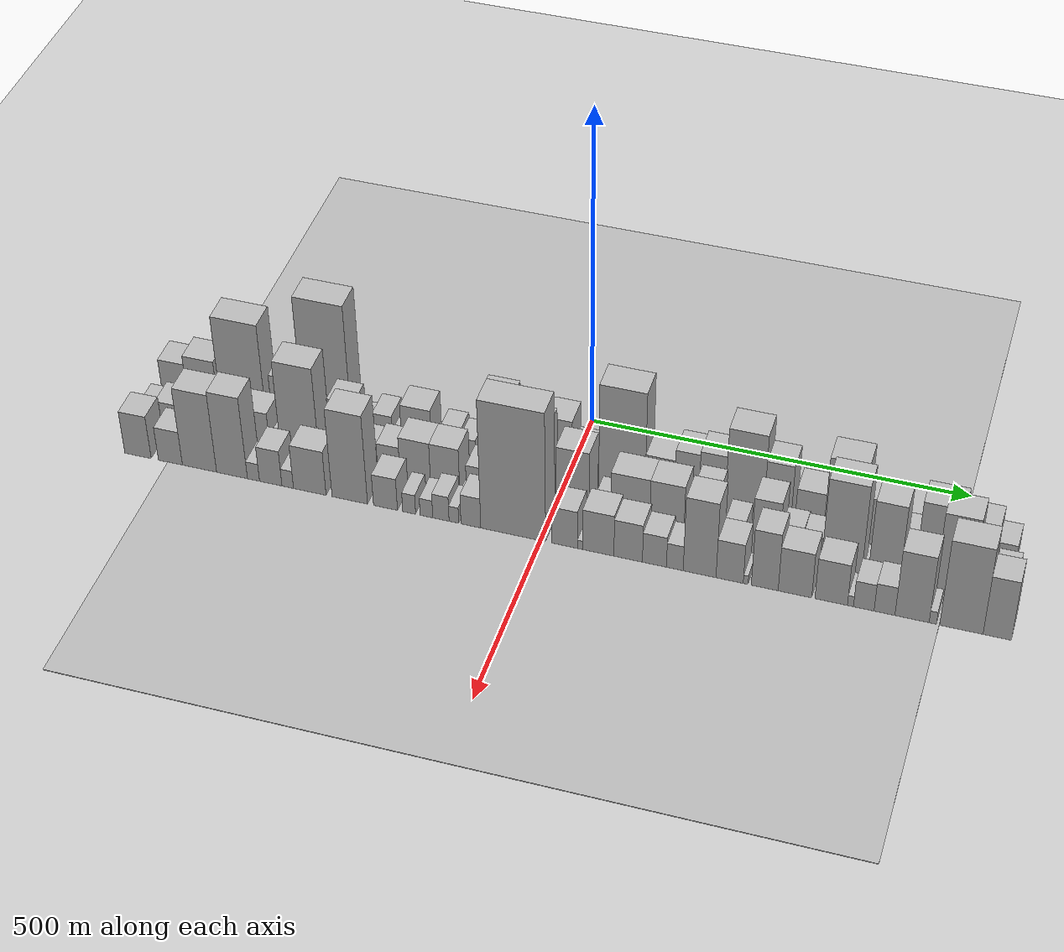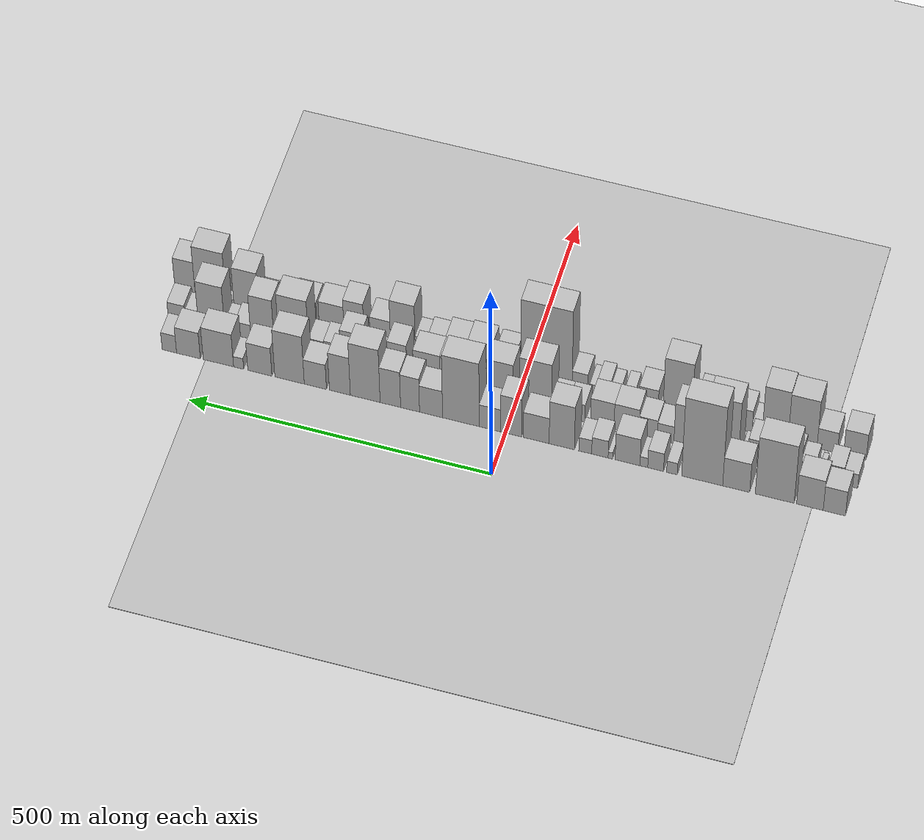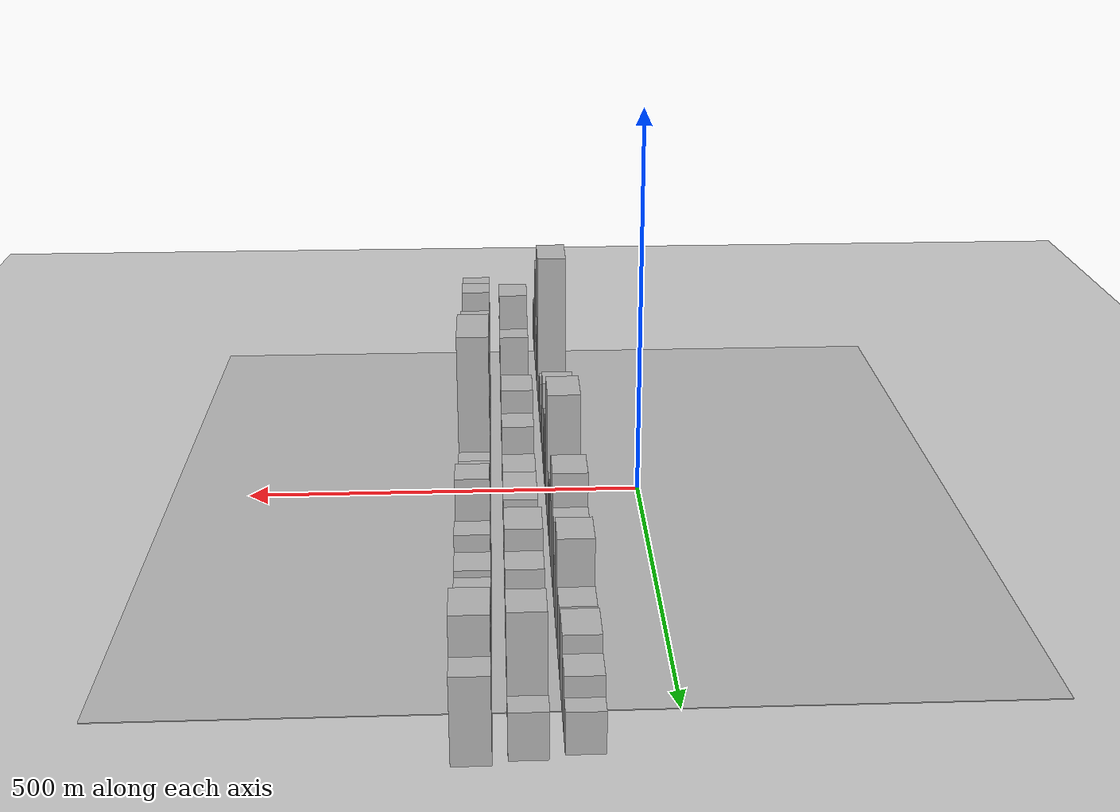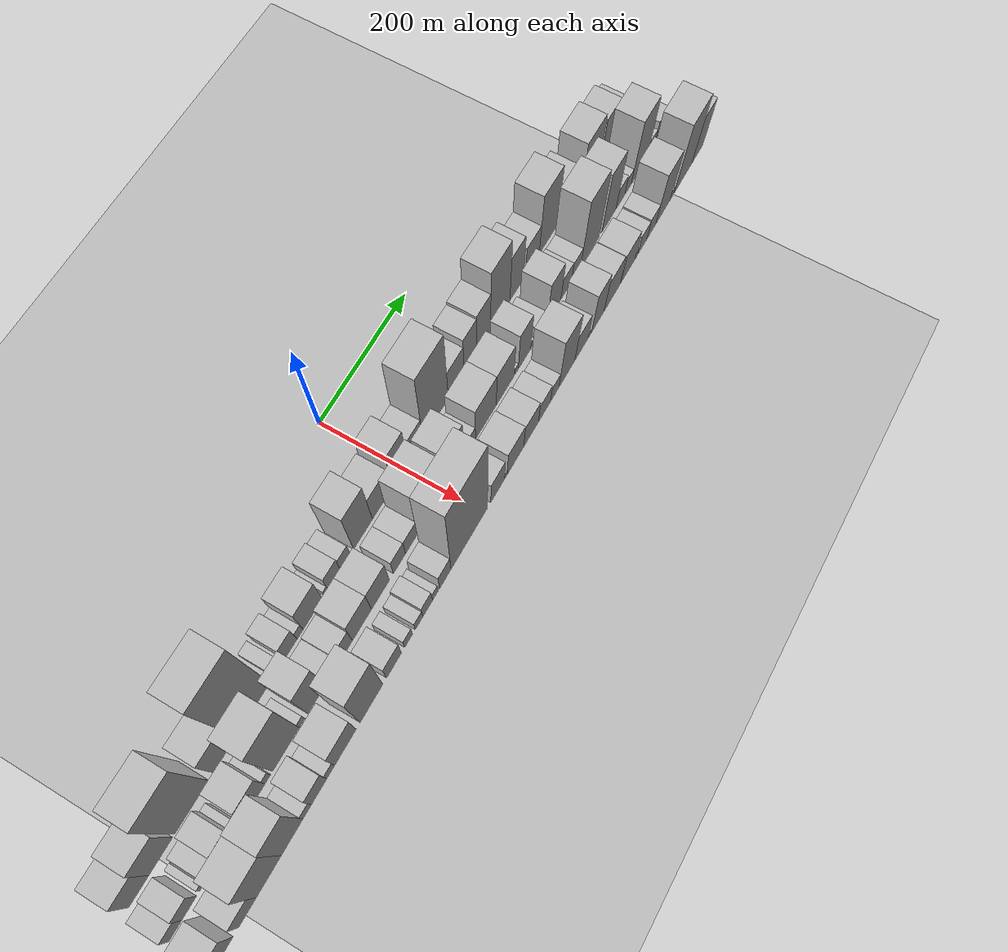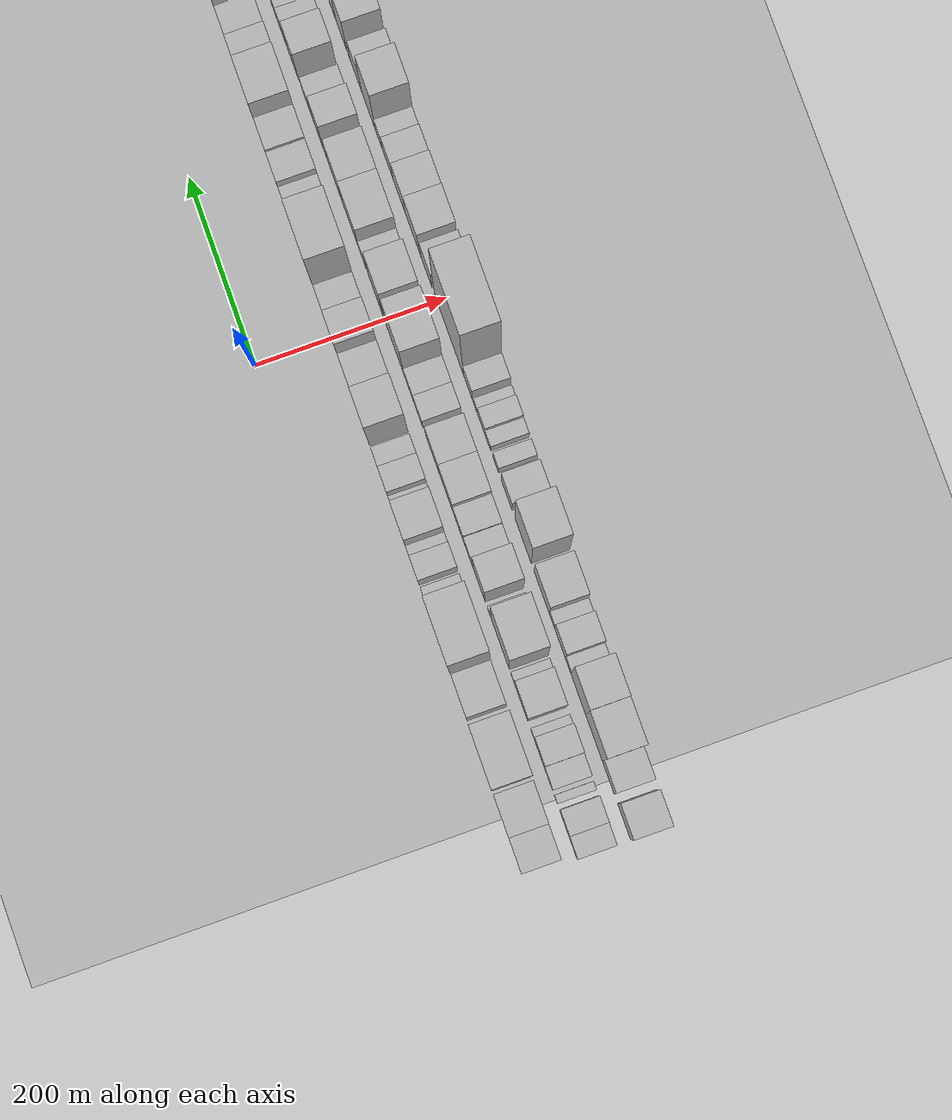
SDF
<?xml version="1.0" encoding="utf-8"?>

<sdf version="1.6">

   <world name="default">

      <gui fullscreen="0">

         <camera name="user_camera">

            <pose>-15 0 4.57585 0 0 0</pose>

            <view_controller>orbit</view_controller>

         </camera>

      </gui>

      <scene>

         <sky>

           <clouds>

             <speed>12</speed>

           </clouds>

         </sky>

         <ambient>0.4 0.4 0.4 1</ambient>

         <background>0.7 0.7 0.7 1</background>

         <shadows>1</shadows>

      </scene>

      <gravity>0 0 -9.8066</gravity>

      <magnetic_field>6e-06 2.3e-05 -4.2e-05</magnetic_field>

      <physics default="0" name="default_physics" type="ode">

         <ode>

            <solver>

               <type>quick</type>

               <iters>10</iters>

               <sor>1.0</sor>

               <use_dynamic_moi_rescaling>0</use_dynamic_moi_rescaling>

            </solver>

            <constraints>

               <cfm>0</cfm>

               <erp>0.2</erp>

               <contact_max_correcting_vel>100</contact_max_correcting_vel>

               <contact_surface_layer>0.001</contact_surface_layer>

            </constraints>

         </ode>

         <max_step_size>0.004</max_step_size>

         <real_time_factor>1</real_time_factor>

         <real_time_update_rate>250</real_time_update_rate>

      </physics>

      <light name="sun" type="directional">

         <cast_shadows>1</cast_shadows>

         <pose>0 0 10 0 0 0</pose>

         <diffuse>0.8 0.8 0.8 1</diffuse>

         <specular>0.2 0.2 0.2 1</specular>

         <attenuation>

            <range>1000</range>

            <constant>0.9</constant>

            <linear>0.01</linear>

            <quadratic>0.001</quadratic>

         </attenuation>

         <direction>-0.5 0.1 -0.9</direction>

      </light>

      <include>

         <name>ground_plane_1</name>

         <uri>model://HANNAS_ground_plane</uri>

         <pose>0 0 0  0 0 0</pose>

      </include>

      <include>

         <name>ground_plane_2</name>

         <uri>model://HANNAS_ground_plane</uri>

         <pose>100 0 0  0 0 0</pose>

      </include>

      <model name="building_1">

         <static>1</static>

         <pose frame="">100.0000 -536.0385 0 0.000000 0.000000 0.000000</pose>

         <link name="link">

            <pose frame="">0 0 34.50 0 0 0</pose>

            <collision name="collision">

               <geometry>

                  <box>

                     <size>40.0000 35.9229 69.0000</size>

                  </box>

               </geometry>

               <max_contacts>10</max_contacts>

               <surface>

                  <contact>

                     <ode/>

                  </contact>

                  <bounce/>

                  <friction>

                     <torsional>

                        <ode/>

                     </torsional>

                     <ode/>

                  </friction>

               </surface>

            </collision>

            <visual name="visual">

               <cast_shadows>0</cast_shadows>

               <geometry>

                  <box>

                     <size>40.0000 35.9229 69.0000</size>

                  </box>

               </geometry>

               <material>

                  <script>

                     <uri>model://HANNAS_wall/materials/scripts</uri>

                     <uri>model://HANNAS_wall/materials/textures</uri>

                     <name>vrc/HANNAS_wall</name>

                  </script>

               </material>

            </visual>

            <self_collide>0</self_collide>

            <enable_wind>0</enable_wind>

            <kinematic>0</kinematic>

         </link>

      </model>

      <model name="building_2">

         <static>1</static>

         <pose frame="">100.0000 -496.5925 0 0.000000 0.000000 0.000000</pose>

         <link name="link">

            <pose frame="">0 0 42.00 0 0 0</pose>

            <collision name="collision">

               <geometry>

                  <box>

                     <size>40.0000 42.9691 84.0000</size>

                  </box>

               </geometry>

               <max_contacts>10</max_contacts>

               <surface>

                  <contact>

                     <ode/>

                  </contact>

                  <bounce/>

                  <friction>

                     <torsional>

                        <ode/>

                     </torsional>

                     <ode/>

                  </friction>

               </surface>

            </collision>

            <visual name="visual">

               <cast_shadows>0</cast_shadows>

               <geometry>

                  <box>

                     <size>40.0000 42.9691 84.0000</size>

                  </box>

               </geometry>

               <material>

                  <script>

                     <uri>model://HANNAS_wall/materials/scripts</uri>

                     <uri>model://HANNAS_wall/materials/textures</uri>

                     <name>vrc/HANNAS_wall</name>

                  </script>

               </material>

            </visual>

            <self_collide>0</self_collide>

            <enable_wind>0</enable_wind>

            <kinematic>0</kinematic>

         </link>

      </model>

      <model name="building_3">

         <static>1</static>

         <pose frame="">100.0000 -439.6321 0 0.000000 0.000000 0.000000</pose>

         <link name="link">

            <pose frame="">0 0 81.00 0 0 0</pose>

            <collision name="collision">

               <geometry>

                  <box>

                     <size>40.0000 62.9518 162.0000</size>

                  </box>

               </geometry>

               <max_contacts>10</max_contacts>

               <surface>

                  <contact>

                     <ode/>

                  </contact>

                  <bounce/>

                  <friction>

                     <torsional>

                        <ode/>

                     </torsional>

                     <ode/>

                  </friction>

               </surface>

            </collision>

            <visual name="visual">

               <cast_shadows>0</cast_shadows>

               <geometry>

                  <box>

                     <size>40.0000 62.9518 162.0000</size>

                  </box>

               </geometry>

               <material>

                  <script>

                     <uri>model://HANNAS_wall/materials/scripts</uri>

                     <uri>model://HANNAS_wall/materials/textures</uri>

                     <name>vrc/HANNAS_wall</name>

                  </script>

               </material>

            </visual>

            <self_collide>0</self_collide>

            <enable_wind>0</enable_wind>

            <kinematic>0</kinematic>

         </link>

      </model>

      <model name="building_4">

         <static>1</static>

         <pose frame="">100.0000 -377.1761 0 0.000000 0.000000 0.000000</pose>

         <link name="link">

            <pose frame="">0 0 40.50 0 0 0</pose>

            <collision name="collision">

               <geometry>

                  <box>

                     <size>40.0000 43.9602 81.0000</size>

                  </box>

               </geometry>

               <max_contacts>10</max_contacts>

               <surface>

                  <contact>

                     <ode/>

                  </contact>

                  <bounce/>

                  <friction>

                     <torsional>

                        <ode/>

                     </torsional>

                     <ode/>

                  </friction>

               </surface>

            </collision>

            <visual name="visual">

               <cast_shadows>0</cast_shadows>

               <geometry>

                  <box>

                     <size>40.0000 43.9602 81.0000</size>

                  </box>

               </geometry>

               <material>

                  <script>

                     <uri>model://HANNAS_wall/materials/scripts</uri>

                     <uri>model://HANNAS_wall/materials/textures</uri>

                     <name>vrc/HANNAS_wall</name>

                  </script>

               </material>

            </visual>

            <self_collide>0</self_collide>

            <enable_wind>0</enable_wind>

            <kinematic>0</kinematic>

         </link>

      </model>

      <model name="building_5">

         <static>1</static>

         <pose frame="">100.0000 -321.7930 0 0.000000 0.000000 0.000000</pose>

         <link name="link">

            <pose frame="">0 0 111.00 0 0 0</pose>

            <collision name="collision">

               <geometry>

                  <box>

                     <size>40.0000 66.8061 222.0000</size>

                  </box>

               </geometry>

               <max_contacts>10</max_contacts>

               <surface>

                  <contact>

                     <ode/>

                  </contact>

                  <bounce/>

                  <friction>

                     <torsional>

                        <ode/>

                     </torsional>

                     <ode/>

                  </friction>

               </surface>

            </collision>

            <visual name="visual">

               <cast_shadows>0</cast_shadows>

               <geometry>

                  <box>

                     <size>40.0000 66.8061 222.0000</size>

                  </box>

               </geometry>

               <material>

                  <script>

                     <uri>model://HANNAS_wall/materials/scripts</uri>

                     <uri>model://HANNAS_wall/materials/textures</uri>

                     <name>vrc/HANNAS_wall</name>

                  </script>

               </material>

            </visual>

            <self_collide>0</self_collide>

            <enable_wind>0</enable_wind>

            <kinematic>0</kinematic>

         </link>

      </model>

      <model name="building_6">

         <static>1</static>

         <pose frame="">100.0000 -272.6790 0 0.000000 0.000000 0.000000</pose>

         <link name="link">

            <pose frame="">0 0 16.50 0 0 0</pose>

            <collision name="collision">

               <geometry>

                  <box>

                     <size>40.0000 17.4219 33.0000</size>

                  </box>

               </geometry>

               <max_contacts>10</max_contacts>

               <surface>

                  <contact>

                     <ode/>

                  </contact>

                  <bounce/>

                  <friction>

                     <torsional>

                        <ode/>

                     </torsional>

                     <ode/>

                  </friction>

               </surface>

            </collision>

            <visual name="visual">

               <cast_shadows>0</cast_shadows>

               <geometry>

                  <box>

                     <size>40.0000 17.4219 33.0000</size>

                  </box>

               </geometry>

               <material>

                  <script>

                     <uri>model://HANNAS_wall/materials/scripts</uri>

                     <uri>model://HANNAS_wall/materials/textures</uri>

                     <name>vrc/HANNAS_wall</name>

                  </script>

               </material>

            </visual>

            <self_collide>0</self_collide>

            <enable_wind>0</enable_wind>

            <kinematic>0</kinematic>

         </link>

      </model>

      <model name="building_7">

         <static>1</static>

         <pose frame="">100.0000 -246.0268 0 0.000000 0.000000 0.000000</pose>

         <link name="link">

            <pose frame="">0 0 25.50 0 0 0</pose>

            <collision name="collision">

               <geometry>

                  <box>

                     <size>40.0000 25.8825 51.0000</size>

                  </box>

               </geometry>

               <max_contacts>10</max_contacts>

               <surface>

                  <contact>

                     <ode/>

                  </contact>

                  <bounce/>

                  <friction>

                     <torsional>

                        <ode/>

                     </torsional>

                     <ode/>

                  </friction>

               </surface>

            </collision>

            <visual name="visual">

               <cast_shadows>0</cast_shadows>

               <geometry>

                  <box>

                     <size>40.0000 25.8825 51.0000</size>

                  </box>

               </geometry>

               <material>

                  <script>

                     <uri>model://HANNAS_wall/materials/scripts</uri>

                     <uri>model://HANNAS_wall/materials/textures</uri>

                     <name>vrc/HANNAS_wall</name>

                  </script>

               </material>

            </visual>

            <self_collide>0</self_collide>

            <enable_wind>0</enable_wind>

            <kinematic>0</kinematic>

         </link>

      </model>

      <model name="building_8">

         <static>1</static>

         <pose frame="">100.0000 -226.8082 0 0.000000 0.000000 0.000000</pose>

         <link name="link">

            <pose frame="">0 0 13.50 0 0 0</pose>

            <collision name="collision">

               <geometry>

                  <box>

                     <size>40.0000 12.5546 27.0000</size>

                  </box>

               </geometry>

               <max_contacts>10</max_contacts>

               <surface>

                  <contact>

                     <ode/>

                  </contact>

                  <bounce/>

                  <friction>

                     <torsional>

                        <ode/>

                     </torsional>

                     <ode/>

                  </friction>

               </surface>

            </collision>

            <visual name="visual">

               <cast_shadows>0</cast_shadows>

               <geometry>

                  <box>

                     <size>40.0000 12.5546 27.0000</size>

                  </box>

               </geometry>

               <material>

                  <script>

                     <uri>model://HANNAS_wall/materials/scripts</uri>

                     <uri>model://HANNAS_wall/materials/textures</uri>

                     <name>vrc/HANNAS_wall</name>

                  </script>

               </material>

            </visual>

            <self_collide>0</self_collide>

            <enable_wind>0</enable_wind>

            <kinematic>0</kinematic>

         </link>

      </model>

      <model name="building_9">

         <static>1</static>

         <pose frame="">100.0000 -200.1987 0 0.000000 0.000000 0.000000</pose>

         <link name="link">

            <pose frame="">0 0 37.50 0 0 0</pose>

            <collision name="collision">

               <geometry>

                  <box>

                     <size>40.0000 40.6645 75.0000</size>

                  </box>

               </geometry>

               <max_contacts>10</max_contacts>

               <surface>

                  <contact>

                     <ode/>

                  </contact>

                  <bounce/>

                  <friction>

                     <torsional>

                        <ode/>

                     </torsional>

                     <ode/>

                  </friction>

               </surface>

            </collision>

            <visual name="visual">

               <cast_shadows>0</cast_shadows>

               <geometry>

                  <box>

                     <size>40.0000 40.6645 75.0000</size>

                  </box>

               </geometry>

               <material>

                  <script>

                     <uri>model://HANNAS_wall/materials/scripts</uri>

                     <uri>model://HANNAS_wall/materials/textures</uri>

                     <name>vrc/HANNAS_wall</name>

                  </script>

               </material>

            </visual>

            <self_collide>0</self_collide>

            <enable_wind>0</enable_wind>

            <kinematic>0</kinematic>

         </link>

      </model>

      <model name="building_10">

         <static>1</static>

         <pose frame="">100.0000 -172.0679 0 0.000000 0.000000 0.000000</pose>

         <link name="link">

            <pose frame="">0 0 9.00 0 0 0</pose>

            <collision name="collision">

               <geometry>

                  <box>

                     <size>40.0000 7.5971 18.0000</size>

                  </box>

               </geometry>

               <max_contacts>10</max_contacts>

               <surface>

                  <contact>

                     <ode/>

                  </contact>

                  <bounce/>

                  <friction>

                     <torsional>

                        <ode/>

                     </torsional>

                     <ode/>

                  </friction>

               </surface>

            </collision>

            <visual name="visual">

               <cast_shadows>0</cast_shadows>

               <geometry>

                  <box>

                     <size>40.0000 7.5971 18.0000</size>

                  </box>

               </geometry>

               <material>

                  <script>

                     <uri>model://HANNAS_wall/materials/scripts</uri>

                     <uri>model://HANNAS_wall/materials/textures</uri>

                     <name>vrc/HANNAS_wall</name>

                  </script>

               </material>

            </visual>

            <self_collide>0</self_collide>

            <enable_wind>0</enable_wind>

            <kinematic>0</kinematic>

         </link>

      </model>

      <model name="building_11">

         <static>1</static>

         <pose frame="">100.0000 -154.8904 0 0.000000 0.000000 0.000000</pose>

         <link name="link">

            <pose frame="">0 0 24.00 0 0 0</pose>

            <collision name="collision">

               <geometry>

                  <box>

                     <size>40.0000 26.7578 48.0000</size>

                  </box>

               </geometry>

               <max_contacts>10</max_contacts>

               <surface>

                  <contact>

                     <ode/>

                  </contact>

                  <bounce/>

                  <friction>

                     <torsional>

                        <ode/>

                     </torsional>

                     <ode/>

                  </friction>

               </surface>

            </collision>

            <visual name="visual">

               <cast_shadows>0</cast_shadows>

               <geometry>

                  <box>

                     <size>40.0000 26.7578 48.0000</size>

                  </box>

               </geometry>

               <material>

                  <script>

                     <uri>model://HANNAS_wall/materials/scripts</uri>

                     <uri>model://HANNAS_wall/materials/textures</uri>

                     <name>vrc/HANNAS_wall</name>

                  </script>

               </material>

            </visual>

            <self_collide>0</self_collide>

            <enable_wind>0</enable_wind>

            <kinematic>0</kinematic>

         </link>

      </model>

      <model name="building_12">

         <static>1</static>

         <pose frame="">100.0000 -130.8595 0 0.000000 0.000000 0.000000</pose>

         <link name="link">

            <pose frame="">0 0 19.50 0 0 0</pose>

            <collision name="collision">

               <geometry>

                  <box>

                     <size>40.0000 21.3041 39.0000</size>

                  </box>

               </geometry>

               <max_contacts>10</max_contacts>

               <surface>

                  <contact>

                     <ode/>

                  </contact>

                  <bounce/>

                  <friction>

                     <torsional>

                        <ode/>

                     </torsional>

                     <ode/>

                  </friction>

               </surface>

            </collision>

            <visual name="visual">

               <cast_shadows>0</cast_shadows>

               <geometry>

                  <box>

                     <size>40.0000 21.3041 39.0000</size>

                  </box>

               </geometry>

               <material>

                  <script>

                     <uri>model://HANNAS_wall/materials/scripts</uri>

                     <uri>model://HANNAS_wall/materials/textures</uri>

                     <name>vrc/HANNAS_wall</name>

                  </script>

               </material>

            </visual>

            <self_collide>0</self_collide>

            <enable_wind>0</enable_wind>

            <kinematic>0</kinematic>

         </link>

      </model>

      <model name="building_13">

         <static>1</static>

         <pose frame="">100.0000 -92.4221 0 0.000000 0.000000 0.000000</pose>

         <link name="link">

            <pose frame="">0 0 60.00 0 0 0</pose>

            <collision name="collision">

               <geometry>

                  <box>

                     <size>40.0000 41.5708 120.0000</size>

                  </box>

               </geometry>

               <max_contacts>10</max_contacts>

               <surface>

                  <contact>

                     <ode/>

                  </contact>

                  <bounce/>

                  <friction>

                     <torsional>

                        <ode/>

                     </torsional>

                     <ode/>

                  </friction>

               </surface>

            </collision>

            <visual name="visual">

               <cast_shadows>0</cast_shadows>

               <geometry>

                  <box>

                     <size>40.0000 41.5708 120.0000</size>

                  </box>

               </geometry>

               <material>

                  <script>

                     <uri>model://HANNAS_wall/materials/scripts</uri>

                     <uri>model://HANNAS_wall/materials/textures</uri>

                     <name>vrc/HANNAS_wall</name>

                  </script>

               </material>

            </visual>

            <self_collide>0</self_collide>

            <enable_wind>0</enable_wind>

            <kinematic>0</kinematic>

         </link>

      </model>

      <model name="building_14">

         <static>1</static>

         <pose frame="">100.0000 -50.4554 0 0.000000 0.000000 0.000000</pose>

         <link name="link">

            <pose frame="">0 0 36.00 0 0 0</pose>

            <collision name="collision">

               <geometry>

                  <box>

                     <size>40.0000 42.3625 72.0000</size>

                  </box>

               </geometry>

               <max_contacts>10</max_contacts>

               <surface>

                  <contact>

                     <ode/>

                  </contact>

                  <bounce/>

                  <friction>

                     <torsional>

                        <ode/>

                     </torsional>

                     <ode/>

                  </friction>

               </surface>

            </collision>

            <visual name="visual">

               <cast_shadows>0</cast_shadows>

               <geometry>

                  <box>

                     <size>40.0000 42.3625 72.0000</size>

                  </box>

               </geometry>

               <material>

                  <script>

                     <uri>model://HANNAS_wall/materials/scripts</uri>

                     <uri>model://HANNAS_wall/materials/textures</uri>

                     <name>vrc/HANNAS_wall</name>

                  </script>

               </material>

            </visual>

            <self_collide>0</self_collide>

            <enable_wind>0</enable_wind>

            <kinematic>0</kinematic>

         </link>

      </model>

      <model name="building_15">

         <static>1</static>

         <pose frame="">100.0000 -8.9203 0 0.000000 0.000000 0.000000</pose>

         <link name="link">

            <pose frame="">0 0 52.50 0 0 0</pose>

            <collision name="collision">

               <geometry>

                  <box>

                     <size>40.0000 34.7076 105.0000</size>

                  </box>

               </geometry>

               <max_contacts>10</max_contacts>

               <surface>

                  <contact>

                     <ode/>

                  </contact>

                  <bounce/>

                  <friction>

                     <torsional>

                        <ode/>

                     </torsional>

                     <ode/>

                  </friction>

               </surface>

            </collision>

            <visual name="visual">

               <cast_shadows>0</cast_shadows>

               <geometry>

                  <box>

                     <size>40.0000 34.7076 105.0000</size>

                  </box>

               </geometry>

               <material>

                  <script>

                     <uri>model://HANNAS_wall/materials/scripts</uri>

                     <uri>model://HANNAS_wall/materials/textures</uri>

                     <name>vrc/HANNAS_wall</name>

                  </script>

               </material>

            </visual>

            <self_collide>0</self_collide>

            <enable_wind>0</enable_wind>

            <kinematic>0</kinematic>

         </link>

      </model>

      <model name="building_16">

         <static>1</static>

         <pose frame="">100.0000 25.9235 0 0.000000 0.000000 0.000000</pose>

         <link name="link">

            <pose frame="">0 0 31.50 0 0 0</pose>

            <collision name="collision">

               <geometry>

                  <box>

                     <size>40.0000 34.9801 63.0000</size>

                  </box>

               </geometry>

               <max_contacts>10</max_contacts>

               <surface>

                  <contact>

                     <ode/>

                  </contact>

                  <bounce/>

                  <friction>

                     <torsional>

                        <ode/>

                     </torsional>

                     <ode/>

                  </friction>

               </surface>

            </collision>

            <visual name="visual">

               <cast_shadows>0</cast_shadows>

               <geometry>

                  <box>

                     <size>40.0000 34.9801 63.0000</size>

                  </box>

               </geometry>

               <material>

                  <script>

                     <uri>model://HANNAS_wall/materials/scripts</uri>

                     <uri>model://HANNAS_wall/materials/textures</uri>

                     <name>vrc/HANNAS_wall</name>

                  </script>

               </material>

            </visual>

            <self_collide>0</self_collide>

            <enable_wind>0</enable_wind>

            <kinematic>0</kinematic>

         </link>

      </model>

      <model name="building_17">

         <static>1</static>

         <pose frame="">100.0000 73.7770 0 0.000000 0.000000 0.000000</pose>

         <link name="link">

            <pose frame="">0 0 88.50 0 0 0</pose>

            <collision name="collision">

               <geometry>

                  <box>

                     <size>40.0000 60.7268 177.0000</size>

                  </box>

               </geometry>

               <max_contacts>10</max_contacts>

               <surface>

                  <contact>

                     <ode/>

                  </contact>

                  <bounce/>

                  <friction>

                     <torsional>

                        <ode/>

                     </torsional>

                     <ode/>

                  </friction>

               </surface>

            </collision>

            <visual name="visual">

               <cast_shadows>0</cast_shadows>

               <geometry>

                  <box>

                     <size>40.0000 60.7268 177.0000</size>

                  </box>

               </geometry>

               <material>

                  <script>

                     <uri>model://HANNAS_wall/materials/scripts</uri>

                     <uri>model://HANNAS_wall/materials/textures</uri>

                     <name>vrc/HANNAS_wall</name>

                  </script>

               </material>

            </visual>

            <self_collide>0</self_collide>

            <enable_wind>0</enable_wind>

            <kinematic>0</kinematic>

         </link>

      </model>

      <model name="building_18">

         <static>1</static>

         <pose frame="">100.0000 123.2803 0 0.000000 0.000000 0.000000</pose>

         <link name="link">

            <pose frame="">0 0 37.50 0 0 0</pose>

            <collision name="collision">

               <geometry>

                  <box>

                     <size>40.0000 38.2798 75.0000</size>

                  </box>

               </geometry>

               <max_contacts>10</max_contacts>

               <surface>

                  <contact>

                     <ode/>

                  </contact>

                  <bounce/>

                  <friction>

                     <torsional>

                        <ode/>

                     </torsional>

                     <ode/>

                  </friction>

               </surface>

            </collision>

            <visual name="visual">

               <cast_shadows>0</cast_shadows>

               <geometry>

                  <box>

                     <size>40.0000 38.2798 75.0000</size>

                  </box>

               </geometry>

               <material>

                  <script>

                     <uri>model://HANNAS_wall/materials/scripts</uri>

                     <uri>model://HANNAS_wall/materials/textures</uri>

                     <name>vrc/HANNAS_wall</name>

                  </script>

               </material>

            </visual>

            <self_collide>0</self_collide>

            <enable_wind>0</enable_wind>

            <kinematic>0</kinematic>

         </link>

      </model>

      <model name="building_19">

         <static>1</static>

         <pose frame="">100.0000 158.1278 0 0.000000 0.000000 0.000000</pose>

         <link name="link">

            <pose frame="">0 0 46.50 0 0 0</pose>

            <collision name="collision">

               <geometry>

                  <box>

                     <size>40.0000 31.4152 93.0000</size>

                  </box>

               </geometry>

               <max_contacts>10</max_contacts>

               <surface>

                  <contact>

                     <ode/>

                  </contact>

                  <bounce/>

                  <friction>

                     <torsional>

                        <ode/>

                     </torsional>

                     <ode/>

                  </friction>

               </surface>

            </collision>

            <visual name="visual">

               <cast_shadows>0</cast_shadows>

               <geometry>

                  <box>

                     <size>40.0000 31.4152 93.0000</size>

                  </box>

               </geometry>

               <material>

                  <script>

                     <uri>model://HANNAS_wall/materials/scripts</uri>

                     <uri>model://HANNAS_wall/materials/textures</uri>

                     <name>vrc/HANNAS_wall</name>

                  </script>

               </material>

            </visual>

            <self_collide>0</self_collide>

            <enable_wind>0</enable_wind>

            <kinematic>0</kinematic>

         </link>

      </model>

      <model name="building_20">

         <static>1</static>

         <pose frame="">100.0000 190.8408 0 0.000000 0.000000 0.000000</pose>

         <link name="link">

            <pose frame="">0 0 49.50 0 0 0</pose>

            <collision name="collision">

               <geometry>

                  <box>

                     <size>40.0000 34.0107 99.0000</size>

                  </box>

               </geometry>

               <max_contacts>10</max_contacts>

               <surface>

                  <contact>

                     <ode/>

                  </contact>

                  <bounce/>

                  <friction>

                     <torsional>

                        <ode/>

                     </torsional>

                     <ode/>

                  </friction>

               </surface>

            </collision>

            <visual name="visual">

               <cast_shadows>0</cast_shadows>

               <geometry>

                  <box>

                     <size>40.0000 34.0107 99.0000</size>

                  </box>

               </geometry>

               <material>

                  <script>

                     <uri>model://HANNAS_wall/materials/scripts</uri>

                     <uri>model://HANNAS_wall/materials/textures</uri>

                     <name>vrc/HANNAS_wall</name>

                  </script>

               </material>

            </visual>

            <self_collide>0</self_collide>

            <enable_wind>0</enable_wind>

            <kinematic>0</kinematic>

         </link>

      </model>

      <model name="building_21">

         <static>1</static>

         <pose frame="">100.0000 232.6172 0 0.000000 0.000000 0.000000</pose>

         <link name="link">

            <pose frame="">0 0 73.50 0 0 0</pose>

            <collision name="collision">

               <geometry>

                  <box>

                     <size>40.0000 49.5420 147.0000</size>

                  </box>

               </geometry>

               <max_contacts>10</max_contacts>

               <surface>

                  <contact>

                     <ode/>

                  </contact>

                  <bounce/>

                  <friction>

                     <torsional>

                        <ode/>

                     </torsional>

                     <ode/>

                  </friction>

               </surface>

            </collision>

            <visual name="visual">

               <cast_shadows>0</cast_shadows>

               <geometry>

                  <box>

                     <size>40.0000 49.5420 147.0000</size>

                  </box>

               </geometry>

               <material>

                  <script>

                     <uri>model://HANNAS_wall/materials/scripts</uri>

                     <uri>model://HANNAS_wall/materials/textures</uri>

                     <name>vrc/HANNAS_wall</name>

                  </script>

               </material>

            </visual>

            <self_collide>0</self_collide>

            <enable_wind>0</enable_wind>

            <kinematic>0</kinematic>

         </link>

      </model>

      <model name="building_22">

         <static>1</static>

         <pose frame="">100.0000 274.8088 0 0.000000 0.000000 0.000000</pose>

         <link name="link">

            <pose frame="">0 0 52.50 0 0 0</pose>

            <collision name="collision">

               <geometry>

                  <box>

                     <size>40.0000 34.8413 105.0000</size>

                  </box>

               </geometry>

               <max_contacts>10</max_contacts>

               <surface>

                  <contact>

                     <ode/>

                  </contact>

                  <bounce/>

                  <friction>

                     <torsional>

                        <ode/>

                     </torsional>

                     <ode/>

                  </friction>

               </surface>

            </collision>

            <visual name="visual">

               <cast_shadows>0</cast_shadows>

               <geometry>

                  <box>

                     <size>40.0000 34.8413 105.0000</size>

                  </box>

               </geometry>

               <material>

                  <script>

                     <uri>model://HANNAS_wall/materials/scripts</uri>

                     <uri>model://HANNAS_wall/materials/textures</uri>

                     <name>vrc/HANNAS_wall</name>

                  </script>

               </material>

            </visual>

            <self_collide>0</self_collide>

            <enable_wind>0</enable_wind>

            <kinematic>0</kinematic>

         </link>

      </model>

      <model name="building_23">

         <static>1</static>

         <pose frame="">100.0000 315.7311 0 0.000000 0.000000 0.000000</pose>

         <link name="link">

            <pose frame="">0 0 34.50 0 0 0</pose>

            <collision name="collision">

               <geometry>

                  <box>

                     <size>40.0000 37.0033 69.0000</size>

                  </box>

               </geometry>

               <max_contacts>10</max_contacts>

               <surface>

                  <contact>

                     <ode/>

                  </contact>

                  <bounce/>

                  <friction>

                     <torsional>

                        <ode/>

                     </torsional>

                     <ode/>

                  </friction>

               </surface>

            </collision>

            <visual name="visual">

               <cast_shadows>0</cast_shadows>

               <geometry>

                  <box>

                     <size>40.0000 37.0033 69.0000</size>

                  </box>

               </geometry>

               <material>

                  <script>

                     <uri>model://HANNAS_wall/materials/scripts</uri>

                     <uri>model://HANNAS_wall/materials/textures</uri>

                     <name>vrc/HANNAS_wall</name>

                  </script>

               </material>

            </visual>

            <self_collide>0</self_collide>

            <enable_wind>0</enable_wind>

            <kinematic>0</kinematic>

         </link>

      </model>

      <model name="building_24">

         <static>1</static>

         <pose frame="">100.0000 358.8089 0 0.000000 0.000000 0.000000</pose>

         <link name="link">

            <pose frame="">0 0 66.00 0 0 0</pose>

            <collision name="collision">

               <geometry>

                  <box>

                     <size>40.0000 49.1523 132.0000</size>

                  </box>

               </geometry>

               <max_contacts>10</max_contacts>

               <surface>

                  <contact>

                     <ode/>

                  </contact>

                  <bounce/>

                  <friction>

                     <torsional>

                        <ode/>

                     </torsional>

                     <ode/>

                  </friction>

               </surface>

            </collision>

            <visual name="visual">

               <cast_shadows>0</cast_shadows>

               <geometry>

                  <box>

                     <size>40.0000 49.1523 132.0000</size>

                  </box>

               </geometry>

               <material>

                  <script>

                     <uri>model://HANNAS_wall/materials/scripts</uri>

                     <uri>model://HANNAS_wall/materials/textures</uri>

                     <name>vrc/HANNAS_wall</name>

                  </script>

               </material>

            </visual>

            <self_collide>0</self_collide>

            <enable_wind>0</enable_wind>

            <kinematic>0</kinematic>

         </link>

      </model>

      <model name="building_25">

         <static>1</static>

         <pose frame="">100.0000 408.5758 0 0.000000 0.000000 0.000000</pose>

         <link name="link">

            <pose frame="">0 0 39.00 0 0 0</pose>

            <collision name="collision">

               <geometry>

                  <box>

                     <size>40.0000 40.3815 78.0000</size>

                  </box>

               </geometry>

               <max_contacts>10</max_contacts>

               <surface>

                  <contact>

                     <ode/>

                  </contact>

                  <bounce/>

                  <friction>

                     <torsional>

                        <ode/>

                     </torsional>

                     <ode/>

                  </friction>

               </surface>

            </collision>

            <visual name="visual">

               <cast_shadows>0</cast_shadows>

               <geometry>

                  <box>

                     <size>40.0000 40.3815 78.0000</size>

                  </box>

               </geometry>

               <material>

                  <script>

                     <uri>model://HANNAS_wall/materials/scripts</uri>

                     <uri>model://HANNAS_wall/materials/textures</uri>

                     <name>vrc/HANNAS_wall</name>

                  </script>

               </material>

            </visual>

            <self_collide>0</self_collide>

            <enable_wind>0</enable_wind>

            <kinematic>0</kinematic>

         </link>

      </model>

      <model name="building_26">

         <static>1</static>

         <pose frame="">100.0000 444.1921 0 0.000000 0.000000 0.000000</pose>

         <link name="link">

            <pose frame="">0 0 15.00 0 0 0</pose>

            <collision name="collision">

               <geometry>

                  <box>

                     <size>40.0000 16.8511 30.0000</size>

                  </box>

               </geometry>

               <max_contacts>10</max_contacts>

               <surface>

                  <contact>

                     <ode/>

                  </contact>

                  <bounce/>

                  <friction>

                     <torsional>

                        <ode/>

                     </torsional>

                     <ode/>

                  </friction>

               </surface>

            </collision>

            <visual name="visual">

               <cast_shadows>0</cast_shadows>

               <geometry>

                  <box>

                     <size>40.0000 16.8511 30.0000</size>

                  </box>

               </geometry>

               <material>

                  <script>

                     <uri>model://HANNAS_wall/materials/scripts</uri>

                     <uri>model://HANNAS_wall/materials/textures</uri>

                     <name>vrc/HANNAS_wall</name>

                  </script>

               </material>

            </visual>

            <self_collide>0</self_collide>

            <enable_wind>0</enable_wind>

            <kinematic>0</kinematic>

         </link>

      </model>

      <model name="building_27">

         <static>1</static>

         <pose frame="">100.0000 478.0710 0 0.000000 0.000000 0.000000</pose>

         <link name="link">

            <pose frame="">0 0 45.00 0 0 0</pose>

            <collision name="collision">

               <geometry>

                  <box>

                     <size>40.0000 50.9065 90.0000</size>

                  </box>

               </geometry>

               <max_contacts>10</max_contacts>

               <surface>

                  <contact>

                     <ode/>

                  </contact>

                  <bounce/>

                  <friction>

                     <torsional>

                        <ode/>

                     </torsional>

                     <ode/>

                  </friction>

               </surface>

            </collision>

            <visual name="visual">

               <cast_shadows>0</cast_shadows>

               <geometry>

                  <box>

                     <size>40.0000 50.9065 90.0000</size>

                  </box>

               </geometry>

               <material>

                  <script>

                     <uri>model://HANNAS_wall/materials/scripts</uri>

                     <uri>model://HANNAS_wall/materials/textures</uri>

                     <name>vrc/HANNAS_wall</name>

                  </script>

               </material>

            </visual>

            <self_collide>0</self_collide>

            <enable_wind>0</enable_wind>

            <kinematic>0</kinematic>

         </link>

      </model>

      <model name="building_28">

         <static>1</static>

         <pose frame="">100.0000 528.5222 0 0.000000 0.000000 0.000000</pose>

         <link name="link">

            <pose frame="">0 0 36.00 0 0 0</pose>

            <collision name="collision">

               <geometry>

                  <box>

                     <size>40.0000 39.9960 72.0000</size>

                  </box>

               </geometry>

               <max_contacts>10</max_contacts>

               <surface>

                  <contact>

                     <ode/>

                  </contact>

                  <bounce/>

                  <friction>

                     <torsional>

                        <ode/>

                     </torsional>

                     <ode/>

                  </friction>

               </surface>

            </collision>

            <visual name="visual">

               <cast_shadows>0</cast_shadows>

               <geometry>

                  <box>

                     <size>40.0000 39.9960 72.0000</size>

                  </box>

               </geometry>

               <material>

                  <script>

                     <uri>model://HANNAS_wall/materials/scripts</uri>

                     <uri>model://HANNAS_wall/materials/textures</uri>

                     <name>vrc/HANNAS_wall</name>

                  </script>

               </material>

            </visual>

            <self_collide>0</self_collide>

            <enable_wind>0</enable_wind>

            <kinematic>0</kinematic>

         </link>

      </model>

      <model name="building_29">

         <static>1</static>

         <pose frame="">100.0000 560.6177 0 0.000000 0.000000 0.000000</pose>

         <link name="link">

            <pose frame="">0 0 24.00 0 0 0</pose>

            <collision name="collision">

               <geometry>

                  <box>

                     <size>40.0000 24.1950 48.0000</size>

                  </box>

               </geometry>

               <max_contacts>10</max_contacts>

               <surface>

                  <contact>

                     <ode/>

                  </contact>

                  <bounce/>

                  <friction>

                     <torsional>

                        <ode/>

                     </torsional>

                     <ode/>

                  </friction>

               </surface>

            </collision>

            <visual name="visual">

               <cast_shadows>0</cast_shadows>

               <geometry>

                  <box>

                     <size>40.0000 24.1950 48.0000</size>

                  </box>

               </geometry>

               <material>

                  <script>

                     <uri>model://HANNAS_wall/materials/scripts</uri>

                     <uri>model://HANNAS_wall/materials/textures</uri>

                     <name>vrc/HANNAS_wall</name>

                  </script>

               </material>

            </visual>

            <self_collide>0</self_collide>

            <enable_wind>0</enable_wind>

            <kinematic>0</kinematic>

         </link>

      </model>

      <model name="building_30">

         <static>1</static>

         <pose frame="">155.0000 -548.3652 0 0.000000 0.000000 0.000000</pose>

         <link name="link">

            <pose frame="">0 0 19.50 0 0 0</pose>

            <collision name="collision">

               <geometry>

                  <box>

                     <size>40.0000 23.2696 39.0000</size>

                  </box>

               </geometry>

               <max_contacts>10</max_contacts>

               <surface>

                  <contact>

                     <ode/>

                  </contact>

                  <bounce/>

                  <friction>

                     <torsional>

                        <ode/>

                     </torsional>

                     <ode/>

                  </friction>

               </surface>

            </collision>

            <visual name="visual">

               <cast_shadows>0</cast_shadows>

               <geometry>

                  <box>

                     <size>40.0000 23.2696 39.0000</size>

                  </box>

               </geometry>

               <material>

                  <script>

                     <uri>model://HANNAS_wall/materials/scripts</uri>

                     <uri>model://HANNAS_wall/materials/textures</uri>

                     <name>vrc/HANNAS_wall</name>

                  </script>

               </material>

            </visual>

            <self_collide>0</self_collide>

            <enable_wind>0</enable_wind>

            <kinematic>0</kinematic>

         </link>

      </model>

      <model name="building_31">

         <static>1</static>

         <pose frame="">155.0000 -523.3684 0 0.000000 0.000000 0.000000</pose>

         <link name="link">

            <pose frame="">0 0 24.00 0 0 0</pose>

            <collision name="collision">

               <geometry>

                  <box>

                     <size>40.0000 26.7240 48.0000</size>

                  </box>

               </geometry>

               <max_contacts>10</max_contacts>

               <surface>

                  <contact>

                     <ode/>

                  </contact>

                  <bounce/>

                  <friction>

                     <torsional>

                        <ode/>

                     </torsional>

                     <ode/>

                  </friction>

               </surface>

            </collision>

            <visual name="visual">

               <cast_shadows>0</cast_shadows>

               <geometry>

                  <box>

                     <size>40.0000 26.7240 48.0000</size>

                  </box>

               </geometry>

               <material>

                  <script>

                     <uri>model://HANNAS_wall/materials/scripts</uri>

                     <uri>model://HANNAS_wall/materials/textures</uri>

                     <name>vrc/HANNAS_wall</name>

                  </script>

               </material>

            </visual>

            <self_collide>0</self_collide>

            <enable_wind>0</enable_wind>

            <kinematic>0</kinematic>

         </link>

      </model>

      <model name="building_32">

         <static>1</static>

         <pose frame="">155.0000 -499.5796 0 0.000000 0.000000 0.000000</pose>

         <link name="link">

            <pose frame="">0 0 9.00 0 0 0</pose>

            <collision name="collision">

               <geometry>

                  <box>

                     <size>40.0000 8.8535 18.0000</size>

                  </box>

               </geometry>

               <max_contacts>10</max_contacts>

               <surface>

                  <contact>

                     <ode/>

                  </contact>

                  <bounce/>

                  <friction>

                     <torsional>

                        <ode/>

                     </torsional>

                     <ode/>

                  </friction>

               </surface>

            </collision>

            <visual name="visual">

               <cast_shadows>0</cast_shadows>

               <geometry>

                  <box>

                     <size>40.0000 8.8535 18.0000</size>

                  </box>

               </geometry>

               <material>

                  <script>

                     <uri>model://HANNAS_wall/materials/scripts</uri>

                     <uri>model://HANNAS_wall/materials/textures</uri>

                     <name>vrc/HANNAS_wall</name>

                  </script>

               </material>

            </visual>

            <self_collide>0</self_collide>

            <enable_wind>0</enable_wind>

            <kinematic>0</kinematic>

         </link>

      </model>

      <model name="building_33">

         <static>1</static>

         <pose frame="">155.0000 -478.4820 0 0.000000 0.000000 0.000000</pose>

         <link name="link">

            <pose frame="">0 0 19.50 0 0 0</pose>

            <collision name="collision">

               <geometry>

                  <box>

                     <size>40.0000 23.3418 39.0000</size>

                  </box>

               </geometry>

               <max_contacts>10</max_contacts>

               <surface>

                  <contact>

                     <ode/>

                  </contact>

                  <bounce/>

                  <friction>

                     <torsional>

                        <ode/>

                     </torsional>

                     <ode/>

                  </friction>

               </surface>

            </collision>

            <visual name="visual">

               <cast_shadows>0</cast_shadows>

               <geometry>

                  <box>

                     <size>40.0000 23.3418 39.0000</size>

                  </box>

               </geometry>

               <material>

                  <script>

                     <uri>model://HANNAS_wall/materials/scripts</uri>

                     <uri>model://HANNAS_wall/materials/textures</uri>

                     <name>vrc/HANNAS_wall</name>

                  </script>

               </material>

            </visual>

            <self_collide>0</self_collide>

            <enable_wind>0</enable_wind>

            <kinematic>0</kinematic>

         </link>

      </model>

      <model name="building_34">

         <static>1</static>

         <pose frame="">155.0000 -451.9781 0 0.000000 0.000000 0.000000</pose>

         <link name="link">

            <pose frame="">0 0 28.50 0 0 0</pose>

            <collision name="collision">

               <geometry>

                  <box>

                     <size>40.0000 29.6658 57.0000</size>

                  </box>

               </geometry>

               <max_contacts>10</max_contacts>

               <surface>

                  <contact>

                     <ode/>

                  </contact>

                  <bounce/>

                  <friction>

                     <torsional>

                        <ode/>

                     </torsional>

                     <ode/>

                  </friction>

               </surface>

            </collision>

            <visual name="visual">

               <cast_shadows>0</cast_shadows>

               <geometry>

                  <box>

                     <size>40.0000 29.6658 57.0000</size>

                  </box>

               </geometry>

               <material>

                  <script>

                     <uri>model://HANNAS_wall/materials/scripts</uri>

                     <uri>model://HANNAS_wall/materials/textures</uri>

                     <name>vrc/HANNAS_wall</name>

                  </script>

               </material>

            </visual>

            <self_collide>0</self_collide>

            <enable_wind>0</enable_wind>

            <kinematic>0</kinematic>

         </link>

      </model>

      <model name="building_35">

         <static>1</static>

         <pose frame="">155.0000 -432.1855 0 0.000000 0.000000 0.000000</pose>

         <link name="link">

            <pose frame="">0 0 12.00 0 0 0</pose>

            <collision name="collision">

               <geometry>

                  <box>

                     <size>40.0000 9.9195 24.0000</size>

                  </box>

               </geometry>

               <max_contacts>10</max_contacts>

               <surface>

                  <contact>

                     <ode/>

                  </contact>

                  <bounce/>

                  <friction>

                     <torsional>

                        <ode/>

                     </torsional>

                     <ode/>

                  </friction>

               </surface>

            </collision>

            <visual name="visual">

               <cast_shadows>0</cast_shadows>

               <geometry>

                  <box>

                     <size>40.0000 9.9195 24.0000</size>

                  </box>

               </geometry>

               <material>

                  <script>

                     <uri>model://HANNAS_wall/materials/scripts</uri>

                     <uri>model://HANNAS_wall/materials/textures</uri>

                     <name>vrc/HANNAS_wall</name>

                  </script>

               </material>

            </visual>

            <self_collide>0</self_collide>

            <enable_wind>0</enable_wind>

            <kinematic>0</kinematic>

         </link>

      </model>

      <model name="building_36">

         <static>1</static>

         <pose frame="">155.0000 -400.0796 0 0.000000 0.000000 0.000000</pose>

         <link name="link">

            <pose frame="">0 0 33.00 0 0 0</pose>

            <collision name="collision">

               <geometry>

                  <box>

                     <size>40.0000 38.2922 66.0000</size>

                  </box>

               </geometry>

               <max_contacts>10</max_contacts>

               <surface>

                  <contact>

                     <ode/>

                  </contact>

                  <bounce/>

                  <friction>

                     <torsional>

                        <ode/>

                     </torsional>

                     <ode/>

                  </friction>

               </surface>

            </collision>

            <visual name="visual">

               <cast_shadows>0</cast_shadows>

               <geometry>

                  <box>

                     <size>40.0000 38.2922 66.0000</size>

                  </box>

               </geometry>

               <material>

                  <script>

                     <uri>model://HANNAS_wall/materials/scripts</uri>

                     <uri>model://HANNAS_wall/materials/textures</uri>

                     <name>vrc/HANNAS_wall</name>

                  </script>

               </material>

            </visual>

            <self_collide>0</self_collide>

            <enable_wind>0</enable_wind>

            <kinematic>0</kinematic>

         </link>

      </model>

      <model name="building_37">

         <static>1</static>

         <pose frame="">155.0000 -375.5021 0 0.000000 0.000000 0.000000</pose>

         <link name="link">

            <pose frame="">0 0 13.50 0 0 0</pose>

            <collision name="collision">

               <geometry>

                  <box>

                     <size>40.0000 10.8628 27.0000</size>

                  </box>

               </geometry>

               <max_contacts>10</max_contacts>

               <surface>

                  <contact>

                     <ode/>

                  </contact>

                  <bounce/>

                  <friction>

                     <torsional>

                        <ode/>

                     </torsional>

                     <ode/>

                  </friction>

               </surface>

            </collision>

            <visual name="visual">

               <cast_shadows>0</cast_shadows>

               <geometry>

                  <box>

                     <size>40.0000 10.8628 27.0000</size>

                  </box>

               </geometry>

               <material>

                  <script>

                     <uri>model://HANNAS_wall/materials/scripts</uri>

                     <uri>model://HANNAS_wall/materials/textures</uri>

                     <name>vrc/HANNAS_wall</name>

                  </script>

               </material>

            </visual>

            <self_collide>0</self_collide>

            <enable_wind>0</enable_wind>

            <kinematic>0</kinematic>

         </link>

      </model>

      <model name="building_38">

         <static>1</static>

         <pose frame="">155.0000 -339.6478 0 0.000000 0.000000 0.000000</pose>

         <link name="link">

            <pose frame="">0 0 79.50 0 0 0</pose>

            <collision name="collision">

               <geometry>

                  <box>

                     <size>40.0000 52.8458 159.0000</size>

                  </box>

               </geometry>

               <max_contacts>10</max_contacts>

               <surface>

                  <contact>

                     <ode/>

                  </contact>

                  <bounce/>

                  <friction>

                     <torsional>

                        <ode/>

                     </torsional>

                     <ode/>

                  </friction>

               </surface>

            </collision>

            <visual name="visual">

               <cast_shadows>0</cast_shadows>

               <geometry>

                  <box>

                     <size>40.0000 52.8458 159.0000</size>

                  </box>

               </geometry>

               <material>

                  <script>

                     <uri>model://HANNAS_wall/materials/scripts</uri>

                     <uri>model://HANNAS_wall/materials/textures</uri>

                     <name>vrc/HANNAS_wall</name>

                  </script>

               </material>

            </visual>

            <self_collide>0</self_collide>

            <enable_wind>0</enable_wind>

            <kinematic>0</kinematic>

         </link>

      </model>

      <model name="building_39">

         <static>1</static>

         <pose frame="">155.0000 -307.6786 0 0.000000 0.000000 0.000000</pose>

         <link name="link">

            <pose frame="">0 0 12.00 0 0 0</pose>

            <collision name="collision">

               <geometry>

                  <box>

                     <size>40.0000 11.0926 24.0000</size>

                  </box>

               </geometry>

               <max_contacts>10</max_contacts>

               <surface>

                  <contact>

                     <ode/>

                  </contact>

                  <bounce/>

                  <friction>

                     <torsional>

                        <ode/>

                     </torsional>

                     <ode/>

                  </friction>

               </surface>

            </collision>

            <visual name="visual">

               <cast_shadows>0</cast_shadows>

               <geometry>

                  <box>

                     <size>40.0000 11.0926 24.0000</size>

                  </box>

               </geometry>

               <material>

                  <script>

                     <uri>model://HANNAS_wall/materials/scripts</uri>

                     <uri>model://HANNAS_wall/materials/textures</uri>

                     <name>vrc/HANNAS_wall</name>

                  </script>

               </material>

            </visual>

            <self_collide>0</self_collide>

            <enable_wind>0</enable_wind>

            <kinematic>0</kinematic>

         </link>

      </model>

      <model name="building_40">

         <static>1</static>

         <pose frame="">155.0000 -278.4249 0 0.000000 0.000000 0.000000</pose>

         <link name="link">

            <pose frame="">0 0 57.00 0 0 0</pose>

            <collision name="collision">

               <geometry>

                  <box>

                     <size>40.0000 35.4147 114.0000</size>

                  </box>

               </geometry>

               <max_contacts>10</max_contacts>

               <surface>

                  <contact>

                     <ode/>

                  </contact>

                  <bounce/>

                  <friction>

                     <torsional>

                        <ode/>

                     </torsional>

                     <ode/>

                  </friction>

               </surface>

            </collision>

            <visual name="visual">

               <cast_shadows>0</cast_shadows>

               <geometry>

                  <box>

                     <size>40.0000 35.4147 114.0000</size>

                  </box>

               </geometry>

               <material>

                  <script>

                     <uri>model://HANNAS_wall/materials/scripts</uri>

                     <uri>model://HANNAS_wall/materials/textures</uri>

                     <name>vrc/HANNAS_wall</name>

                  </script>

               </material>

            </visual>

            <self_collide>0</self_collide>

            <enable_wind>0</enable_wind>

            <kinematic>0</kinematic>

         </link>

      </model>

      <model name="building_41">

         <static>1</static>

         <pose frame="">155.0000 -247.2422 0 0.000000 0.000000 0.000000</pose>

         <link name="link">

            <pose frame="">0 0 24.00 0 0 0</pose>

            <collision name="collision">

               <geometry>

                  <box>

                     <size>40.0000 26.9508 48.0000</size>

                  </box>

               </geometry>

               <max_contacts>10</max_contacts>

               <surface>

                  <contact>

                     <ode/>

                  </contact>

                  <bounce/>

                  <friction>

                     <torsional>

                        <ode/>

                     </torsional>

                     <ode/>

                  </friction>

               </surface>

            </collision>

            <visual name="visual">

               <cast_shadows>0</cast_shadows>

               <geometry>

                  <box>

                     <size>40.0000 26.9508 48.0000</size>

                  </box>

               </geometry>

               <material>

                  <script>

                     <uri>model://HANNAS_wall/materials/scripts</uri>

                     <uri>model://HANNAS_wall/materials/textures</uri>

                     <name>vrc/HANNAS_wall</name>

                  </script>

               </material>

            </visual>

            <self_collide>0</self_collide>

            <enable_wind>0</enable_wind>

            <kinematic>0</kinematic>

         </link>

      </model>

      <model name="building_42">

         <static>1</static>

         <pose frame="">155.0000 -218.7547 0 0.000000 0.000000 0.000000</pose>

         <link name="link">

            <pose frame="">0 0 27.00 0 0 0</pose>

            <collision name="collision">

               <geometry>

                  <box>

                     <size>40.0000 30.0242 54.0000</size>

                  </box>

               </geometry>

               <max_contacts>10</max_contacts>

               <surface>

                  <contact>

                     <ode/>

                  </contact>

                  <bounce/>

                  <friction>

                     <torsional>

                        <ode/>

                     </torsional>

                     <ode/>

                  </friction>

               </surface>

            </collision>

            <visual name="visual">

               <cast_shadows>0</cast_shadows>

               <geometry>

                  <box>

                     <size>40.0000 30.0242 54.0000</size>

                  </box>

               </geometry>

               <material>

                  <script>

                     <uri>model://HANNAS_wall/materials/scripts</uri>

                     <uri>model://HANNAS_wall/materials/textures</uri>

                     <name>vrc/HANNAS_wall</name>

                  </script>

               </material>

            </visual>

            <self_collide>0</self_collide>

            <enable_wind>0</enable_wind>

            <kinematic>0</kinematic>

         </link>

      </model>

      <model name="building_43">

         <static>1</static>

         <pose frame="">155.0000 -183.2637 0 0.000000 0.000000 0.000000</pose>

         <link name="link">

            <pose frame="">0 0 36.00 0 0 0</pose>

            <collision name="collision">

               <geometry>

                  <box>

                     <size>40.0000 40.9579 72.0000</size>

                  </box>

               </geometry>

               <max_contacts>10</max_contacts>

               <surface>

                  <contact>

                     <ode/>

                  </contact>

                  <bounce/>

                  <friction>

                     <torsional>

                        <ode/>

                     </torsional>

                     <ode/>

                  </friction>

               </surface>

            </collision>

            <visual name="visual">

               <cast_shadows>0</cast_shadows>

               <geometry>

                  <box>

                     <size>40.0000 40.9579 72.0000</size>

                  </box>

               </geometry>

               <material>

                  <script>

                     <uri>model://HANNAS_wall/materials/scripts</uri>

                     <uri>model://HANNAS_wall/materials/textures</uri>

                     <name>vrc/HANNAS_wall</name>

                  </script>

               </material>

            </visual>

            <self_collide>0</self_collide>

            <enable_wind>0</enable_wind>

            <kinematic>0</kinematic>

         </link>

      </model>

      <model name="building_44">

         <static>1</static>

         <pose frame="">155.0000 -143.3269 0 0.000000 0.000000 0.000000</pose>

         <link name="link">

            <pose frame="">0 0 36.00 0 0 0</pose>

            <collision name="collision">

               <geometry>

                  <box>

                     <size>40.0000 38.9156 72.0000</size>

                  </box>

               </geometry>

               <max_contacts>10</max_contacts>

               <surface>

                  <contact>

                     <ode/>

                  </contact>

                  <bounce/>

                  <friction>

                     <torsional>

                        <ode/>

                     </torsional>

                     <ode/>

                  </friction>

               </surface>

            </collision>

            <visual name="visual">

               <cast_shadows>0</cast_shadows>

               <geometry>

                  <box>

                     <size>40.0000 38.9156 72.0000</size>

                  </box>

               </geometry>

               <material>

                  <script>

                     <uri>model://HANNAS_wall/materials/scripts</uri>

                     <uri>model://HANNAS_wall/materials/textures</uri>

                     <name>vrc/HANNAS_wall</name>

                  </script>

               </material>

            </visual>

            <self_collide>0</self_collide>

            <enable_wind>0</enable_wind>

            <kinematic>0</kinematic>

         </link>

      </model>

      <model name="building_45">

         <static>1</static>

         <pose frame="">155.0000 -101.4629 0 0.000000 0.000000 0.000000</pose>

         <link name="link">

            <pose frame="">0 0 24.00 0 0 0</pose>

            <collision name="collision">

               <geometry>

                  <box>

                     <size>40.0000 26.8125 48.0000</size>

                  </box>

               </geometry>

               <max_contacts>10</max_contacts>

               <surface>

                  <contact>

                     <ode/>

                  </contact>

                  <bounce/>

                  <friction>

                     <torsional>

                        <ode/>

                     </torsional>

                     <ode/>

                  </friction>

               </surface>

            </collision>

            <visual name="visual">

               <cast_shadows>0</cast_shadows>

               <geometry>

                  <box>

                     <size>40.0000 26.8125 48.0000</size>

                  </box>

               </geometry>

               <material>

                  <script>

                     <uri>model://HANNAS_wall/materials/scripts</uri>

                     <uri>model://HANNAS_wall/materials/textures</uri>

                     <name>vrc/HANNAS_wall</name>

                  </script>

               </material>

            </visual>

            <self_collide>0</self_collide>

            <enable_wind>0</enable_wind>

            <kinematic>0</kinematic>

         </link>

      </model>

      <model name="building_46">

         <static>1</static>

         <pose frame="">155.0000 -74.0277 0 0.000000 0.000000 0.000000</pose>

         <link name="link">

            <pose frame="">0 0 24.00 0 0 0</pose>

            <collision name="collision">

               <geometry>

                  <box>

                     <size>40.0000 28.0579 48.0000</size>

                  </box>

               </geometry>

               <max_contacts>10</max_contacts>

               <surface>

                  <contact>

                     <ode/>

                  </contact>

                  <bounce/>

                  <friction>

                     <torsional>

                        <ode/>

                     </torsional>

                     <ode/>

                  </friction>

               </surface>

            </collision>

            <visual name="visual">

               <cast_shadows>0</cast_shadows>

               <geometry>

                  <box>

                     <size>40.0000 28.0579 48.0000</size>

                  </box>

               </geometry>

               <material>

                  <script>

                     <uri>model://HANNAS_wall/materials/scripts</uri>

                     <uri>model://HANNAS_wall/materials/textures</uri>

                     <name>vrc/HANNAS_wall</name>

                  </script>

               </material>

            </visual>

            <self_collide>0</self_collide>

            <enable_wind>0</enable_wind>

            <kinematic>0</kinematic>

         </link>

      </model>

      <model name="building_47">

         <static>1</static>

         <pose frame="">155.0000 -33.2867 0 0.000000 0.000000 0.000000</pose>

         <link name="link">

            <pose frame="">0 0 69.00 0 0 0</pose>

            <collision name="collision">

               <geometry>

                  <box>

                     <size>40.0000 53.4242 138.0000</size>

                  </box>

               </geometry>

               <max_contacts>10</max_contacts>

               <surface>

                  <contact>

                     <ode/>

                  </contact>

                  <bounce/>

                  <friction>

                     <torsional>

                        <ode/>

                     </torsional>

                     <ode/>

                  </friction>

               </surface>

            </collision>

            <visual name="visual">

               <cast_shadows>0</cast_shadows>

               <geometry>

                  <box>

                     <size>40.0000 53.4242 138.0000</size>

                  </box>

               </geometry>

               <material>

                  <script>

                     <uri>model://HANNAS_wall/materials/scripts</uri>

                     <uri>model://HANNAS_wall/materials/textures</uri>

                     <name>vrc/HANNAS_wall</name>

                  </script>

               </material>

            </visual>

            <self_collide>0</self_collide>

            <enable_wind>0</enable_wind>

            <kinematic>0</kinematic>

         </link>

      </model>

      <model name="building_48">

         <static>1</static>

         <pose frame="">155.0000 25.0939 0 0.000000 0.000000 0.000000</pose>

         <link name="link">

            <pose frame="">0 0 55.50 0 0 0</pose>

            <collision name="collision">

               <geometry>

                  <box>

                     <size>40.0000 43.3369 111.0000</size>

                  </box>

               </geometry>

               <max_contacts>10</max_contacts>

               <surface>

                  <contact>

                     <ode/>

                  </contact>

                  <bounce/>

                  <friction>

                     <torsional>

                        <ode/>

                     </torsional>

                     <ode/>

                  </friction>

               </surface>

            </collision>

            <visual name="visual">

               <cast_shadows>0</cast_shadows>

               <geometry>

                  <box>

                     <size>40.0000 43.3369 111.0000</size>

                  </box>

               </geometry>

               <material>

                  <script>

                     <uri>model://HANNAS_wall/materials/scripts</uri>

                     <uri>model://HANNAS_wall/materials/textures</uri>

                     <name>vrc/HANNAS_wall</name>

                  </script>

               </material>

            </visual>

            <self_collide>0</self_collide>

            <enable_wind>0</enable_wind>

            <kinematic>0</kinematic>

         </link>

      </model>

      <model name="building_49">

         <static>1</static>

         <pose frame="">155.0000 64.1573 0 0.000000 0.000000 0.000000</pose>

         <link name="link">

            <pose frame="">0 0 19.50 0 0 0</pose>

            <collision name="collision">

               <geometry>

                  <box>

                     <size>40.0000 20.7899 39.0000</size>

                  </box>

               </geometry>

               <max_contacts>10</max_contacts>

               <surface>

                  <contact>

                     <ode/>

                  </contact>

                  <bounce/>

                  <friction>

                     <torsional>

                        <ode/>

                     </torsional>

                     <ode/>

                  </friction>

               </surface>

            </collision>

            <visual name="visual">

               <cast_shadows>0</cast_shadows>

               <geometry>

                  <box>

                     <size>40.0000 20.7899 39.0000</size>

                  </box>

               </geometry>

               <material>

                  <script>

                     <uri>model://HANNAS_wall/materials/scripts</uri>

                     <uri>model://HANNAS_wall/materials/textures</uri>

                     <name>vrc/HANNAS_wall</name>

                  </script>

               </material>

            </visual>

            <self_collide>0</self_collide>

            <enable_wind>0</enable_wind>

            <kinematic>0</kinematic>

         </link>

      </model>

      <model name="building_50">

         <static>1</static>

         <pose frame="">155.0000 99.8147 0 0.000000 0.000000 0.000000</pose>

         <link name="link">

            <pose frame="">0 0 43.50 0 0 0</pose>

            <collision name="collision">

               <geometry>

                  <box>

                     <size>40.0000 50.5249 87.0000</size>

                  </box>

               </geometry>

               <max_contacts>10</max_contacts>

               <surface>

                  <contact>

                     <ode/>

                  </contact>

                  <bounce/>

                  <friction>

                     <torsional>

                        <ode/>

                     </torsional>

                     <ode/>

                  </friction>

               </surface>

            </collision>

            <visual name="visual">

               <cast_shadows>0</cast_shadows>

               <geometry>

                  <box>

                     <size>40.0000 50.5249 87.0000</size>

                  </box>

               </geometry>

               <material>

                  <script>

                     <uri>model://HANNAS_wall/materials/scripts</uri>

                     <uri>model://HANNAS_wall/materials/textures</uri>

                     <name>vrc/HANNAS_wall</name>

                  </script>

               </material>

            </visual>

            <self_collide>0</self_collide>

            <enable_wind>0</enable_wind>

            <kinematic>0</kinematic>

         </link>

      </model>

      <model name="building_51">

         <static>1</static>

         <pose frame="">155.0000 147.0566 0 0.000000 0.000000 0.000000</pose>

         <link name="link">

            <pose frame="">0 0 43.50 0 0 0</pose>

            <collision name="collision">

               <geometry>

                  <box>

                     <size>40.0000 43.9590 87.0000</size>

                  </box>

               </geometry>

               <max_contacts>10</max_contacts>

               <surface>

                  <contact>

                     <ode/>

                  </contact>

                  <bounce/>

                  <friction>

                     <torsional>

                        <ode/>

                     </torsional>

                     <ode/>

                  </friction>

               </surface>

            </collision>

            <visual name="visual">

               <cast_shadows>0</cast_shadows>

               <geometry>

                  <box>

                     <size>40.0000 43.9590 87.0000</size>

                  </box>

               </geometry>

               <material>

                  <script>

                     <uri>model://HANNAS_wall/materials/scripts</uri>

                     <uri>model://HANNAS_wall/materials/textures</uri>

                     <name>vrc/HANNAS_wall</name>

                  </script>

               </material>

            </visual>

            <self_collide>0</self_collide>

            <enable_wind>0</enable_wind>

            <kinematic>0</kinematic>

         </link>

      </model>

      <model name="building_52">

         <static>1</static>

         <pose frame="">155.0000 175.9386 0 0.000000 0.000000 0.000000</pose>

         <link name="link">

            <pose frame="">0 0 9.00 0 0 0</pose>

            <collision name="collision">

               <geometry>

                  <box>

                     <size>40.0000 7.8050 18.0000</size>

                  </box>

               </geometry>

               <max_contacts>10</max_contacts>

               <surface>

                  <contact>

                     <ode/>

                  </contact>

                  <bounce/>

                  <friction>

                     <torsional>

                        <ode/>

                     </torsional>

                     <ode/>

                  </friction>

               </surface>

            </collision>

            <visual name="visual">

               <cast_shadows>0</cast_shadows>

               <geometry>

                  <box>

                     <size>40.0000 7.8050 18.0000</size>

                  </box>

               </geometry>

               <material>

                  <script>

                     <uri>model://HANNAS_wall/materials/scripts</uri>

                     <uri>model://HANNAS_wall/materials/textures</uri>

                     <name>vrc/HANNAS_wall</name>

                  </script>

               </material>

            </visual>

            <self_collide>0</self_collide>

            <enable_wind>0</enable_wind>

            <kinematic>0</kinematic>

         </link>

      </model>

      <model name="building_53">

         <static>1</static>

         <pose frame="">155.0000 195.8694 0 0.000000 0.000000 0.000000</pose>

         <link name="link">

            <pose frame="">0 0 46.50 0 0 0</pose>

            <collision name="collision">

               <geometry>

                  <box>

                     <size>40.0000 32.0566 93.0000</size>

                  </box>

               </geometry>

               <max_contacts>10</max_contacts>

               <surface>

                  <contact>

                     <ode/>

                  </contact>

                  <bounce/>

                  <friction>

                     <torsional>

                        <ode/>

                     </torsional>

                     <ode/>

                  </friction>

               </surface>

            </collision>

            <visual name="visual">

               <cast_shadows>0</cast_shadows>

               <geometry>

                  <box>

                     <size>40.0000 32.0566 93.0000</size>

                  </box>

               </geometry>

               <material>

                  <script>

                     <uri>model://HANNAS_wall/materials/scripts</uri>

                     <uri>model://HANNAS_wall/materials/textures</uri>

                     <name>vrc/HANNAS_wall</name>

                  </script>

               </material>

            </visual>

            <self_collide>0</self_collide>

            <enable_wind>0</enable_wind>

            <kinematic>0</kinematic>

         </link>

      </model>

      <model name="building_54">

         <static>1</static>

         <pose frame="">155.0000 216.0063 0 0.000000 0.000000 0.000000</pose>

         <link name="link">

            <pose frame="">0 0 9.00 0 0 0</pose>

            <collision name="collision">

               <geometry>

                  <box>

                     <size>40.0000 8.2171 18.0000</size>

                  </box>

               </geometry>

               <max_contacts>10</max_contacts>

               <surface>

                  <contact>

                     <ode/>

                  </contact>

                  <bounce/>

                  <friction>

                     <torsional>

                        <ode/>

                     </torsional>

                     <ode/>

                  </friction>

               </surface>

            </collision>

            <visual name="visual">

               <cast_shadows>0</cast_shadows>

               <geometry>

                  <box>

                     <size>40.0000 8.2171 18.0000</size>

                  </box>

               </geometry>

               <material>

                  <script>

                     <uri>model://HANNAS_wall/materials/scripts</uri>

                     <uri>model://HANNAS_wall/materials/textures</uri>

                     <name>vrc/HANNAS_wall</name>

                  </script>

               </material>

            </visual>

            <self_collide>0</self_collide>

            <enable_wind>0</enable_wind>

            <kinematic>0</kinematic>

         </link>

      </model>

      <model name="building_55">

         <static>1</static>

         <pose frame="">155.0000 233.1701 0 0.000000 0.000000 0.000000</pose>

         <link name="link">

            <pose frame="">0 0 22.50 0 0 0</pose>

            <collision name="collision">

               <geometry>

                  <box>

                     <size>40.0000 26.1104 45.0000</size>

                  </box>

               </geometry>

               <max_contacts>10</max_contacts>

               <surface>

                  <contact>

                     <ode/>

                  </contact>

                  <bounce/>

                  <friction>

                     <torsional>

                        <ode/>

                     </torsional>

                     <ode/>

                  </friction>

               </surface>

            </collision>

            <visual name="visual">

               <cast_shadows>0</cast_shadows>

               <geometry>

                  <box>

                     <size>40.0000 26.1104 45.0000</size>

                  </box>

               </geometry>

               <material>

                  <script>

                     <uri>model://HANNAS_wall/materials/scripts</uri>

                     <uri>model://HANNAS_wall/materials/textures</uri>

                     <name>vrc/HANNAS_wall</name>

                  </script>

               </material>

            </visual>

            <self_collide>0</self_collide>

            <enable_wind>0</enable_wind>

            <kinematic>0</kinematic>

         </link>

      </model>

      <model name="building_56">

         <static>1</static>

         <pose frame="">155.0000 272.7713 0 0.000000 0.000000 0.000000</pose>

         <link name="link">

            <pose frame="">0 0 46.50 0 0 0</pose>

            <collision name="collision">

               <geometry>

                  <box>

                     <size>40.0000 35.0920 93.0000</size>

                  </box>

               </geometry>

               <max_contacts>10</max_contacts>

               <surface>

                  <contact>

                     <ode/>

                  </contact>

                  <bounce/>

                  <friction>

                     <torsional>

                        <ode/>

                     </torsional>

                     <ode/>

                  </friction>

               </surface>

            </collision>

            <visual name="visual">

               <cast_shadows>0</cast_shadows>

               <geometry>

                  <box>

                     <size>40.0000 35.0920 93.0000</size>

                  </box>

               </geometry>

               <material>

                  <script>

                     <uri>model://HANNAS_wall/materials/scripts</uri>

                     <uri>model://HANNAS_wall/materials/textures</uri>

                     <name>vrc/HANNAS_wall</name>

                  </script>

               </material>

            </visual>

            <self_collide>0</self_collide>

            <enable_wind>0</enable_wind>

            <kinematic>0</kinematic>

         </link>

      </model>

      <model name="building_57">

         <static>1</static>

         <pose frame="">155.0000 304.2109 0 0.000000 0.000000 0.000000</pose>

         <link name="link">

            <pose frame="">0 0 25.50 0 0 0</pose>

            <collision name="collision">

               <geometry>

                  <box>

                     <size>40.0000 27.7874 51.0000</size>

                  </box>

               </geometry>

               <max_contacts>10</max_contacts>

               <surface>

                  <contact>

                     <ode/>

                  </contact>

                  <bounce/>

                  <friction>

                     <torsional>

                        <ode/>

                     </torsional>

                     <ode/>

                  </friction>

               </surface>

            </collision>

            <visual name="visual">

               <cast_shadows>0</cast_shadows>

               <geometry>

                  <box>

                     <size>40.0000 27.7874 51.0000</size>

                  </box>

               </geometry>

               <material>

                  <script>

                     <uri>model://HANNAS_wall/materials/scripts</uri>

                     <uri>model://HANNAS_wall/materials/textures</uri>

                     <name>vrc/HANNAS_wall</name>

                  </script>

               </material>

            </visual>

            <self_collide>0</self_collide>

            <enable_wind>0</enable_wind>

            <kinematic>0</kinematic>

         </link>

      </model>

      <model name="building_58">

         <static>1</static>

         <pose frame="">155.0000 330.7806 0 0.000000 0.000000 0.000000</pose>

         <link name="link">

            <pose frame="">0 0 24.00 0 0 0</pose>

            <collision name="collision">

               <geometry>

                  <box>

                     <size>40.0000 25.3520 48.0000</size>

                  </box>

               </geometry>

               <max_contacts>10</max_contacts>

               <surface>

                  <contact>

                     <ode/>

                  </contact>

                  <bounce/>

                  <friction>

                     <torsional>

                        <ode/>

                     </torsional>

                     <ode/>

                  </friction>

               </surface>

            </collision>

            <visual name="visual">

               <cast_shadows>0</cast_shadows>

               <geometry>

                  <box>

                     <size>40.0000 25.3520 48.0000</size>

                  </box>

               </geometry>

               <material>

                  <script>

                     <uri>model://HANNAS_wall/materials/scripts</uri>

                     <uri>model://HANNAS_wall/materials/textures</uri>

                     <name>vrc/HANNAS_wall</name>

                  </script>

               </material>

            </visual>

            <self_collide>0</self_collide>

            <enable_wind>0</enable_wind>

            <kinematic>0</kinematic>

         </link>

      </model>

      <model name="building_59">

         <static>1</static>

         <pose frame="">155.0000 368.5979 0 0.000000 0.000000 0.000000</pose>

         <link name="link">

            <pose frame="">0 0 75.00 0 0 0</pose>

            <collision name="collision">

               <geometry>

                  <box>

                     <size>40.0000 50.2825 150.0000</size>

                  </box>

               </geometry>

               <max_contacts>10</max_contacts>

               <surface>

                  <contact>

                     <ode/>

                  </contact>

                  <bounce/>

                  <friction>

                     <torsional>

                        <ode/>

                     </torsional>

                     <ode/>

                  </friction>

               </surface>

            </collision>

            <visual name="visual">

               <cast_shadows>0</cast_shadows>

               <geometry>

                  <box>

                     <size>40.0000 50.2825 150.0000</size>

                  </box>

               </geometry>

               <material>

                  <script>

                     <uri>model://HANNAS_wall/materials/scripts</uri>

                     <uri>model://HANNAS_wall/materials/textures</uri>

                     <name>vrc/HANNAS_wall</name>

                  </script>

               </material>

            </visual>

            <self_collide>0</self_collide>

            <enable_wind>0</enable_wind>

            <kinematic>0</kinematic>

         </link>

      </model>

      <model name="building_60">

         <static>1</static>

         <pose frame="">155.0000 421.3040 0 0.000000 0.000000 0.000000</pose>

         <link name="link">

            <pose frame="">0 0 64.50 0 0 0</pose>

            <collision name="collision">

               <geometry>

                  <box>

                     <size>40.0000 39.1298 129.0000</size>

                  </box>

               </geometry>

               <max_contacts>10</max_contacts>

               <surface>

                  <contact>

                     <ode/>

                  </contact>

                  <bounce/>

                  <friction>

                     <torsional>

                        <ode/>

                     </torsional>

                     <ode/>

                  </friction>

               </surface>

            </collision>

            <visual name="visual">

               <cast_shadows>0</cast_shadows>

               <geometry>

                  <box>

                     <size>40.0000 39.1298 129.0000</size>

                  </box>

               </geometry>

               <material>

                  <script>

                     <uri>model://HANNAS_wall/materials/scripts</uri>

                     <uri>model://HANNAS_wall/materials/textures</uri>

                     <name>vrc/HANNAS_wall</name>

                  </script>

               </material>

            </visual>

            <self_collide>0</self_collide>

            <enable_wind>0</enable_wind>

            <kinematic>0</kinematic>

         </link>

      </model>

      <model name="building_61">

         <static>1</static>

         <pose frame="">155.0000 453.6986 0 0.000000 0.000000 0.000000</pose>

         <link name="link">

            <pose frame="">0 0 22.50 0 0 0</pose>

            <collision name="collision">

               <geometry>

                  <box>

                     <size>40.0000 25.6594 45.0000</size>

                  </box>

               </geometry>

               <max_contacts>10</max_contacts>

               <surface>

                  <contact>

                     <ode/>

                  </contact>

                  <bounce/>

                  <friction>

                     <torsional>

                        <ode/>

                     </torsional>

                     <ode/>

                  </friction>

               </surface>

            </collision>

            <visual name="visual">

               <cast_shadows>0</cast_shadows>

               <geometry>

                  <box>

                     <size>40.0000 25.6594 45.0000</size>

                  </box>

               </geometry>

               <material>

                  <script>

                     <uri>model://HANNAS_wall/materials/scripts</uri>

                     <uri>model://HANNAS_wall/materials/textures</uri>

                     <name>vrc/HANNAS_wall</name>

                  </script>

               </material>

            </visual>

            <self_collide>0</self_collide>

            <enable_wind>0</enable_wind>

            <kinematic>0</kinematic>

         </link>

      </model>

      <model name="building_62">

         <static>1</static>

         <pose frame="">155.0000 475.5617 0 0.000000 0.000000 0.000000</pose>

         <link name="link">

            <pose frame="">0 0 18.00 0 0 0</pose>

            <collision name="collision">

               <geometry>

                  <box>

                     <size>40.0000 18.0668 36.0000</size>

                  </box>

               </geometry>

               <max_contacts>10</max_contacts>

               <surface>

                  <contact>

                     <ode/>

                  </contact>

                  <bounce/>

                  <friction>

                     <torsional>

                        <ode/>

                     </torsional>

                     <ode/>

                  </friction>

               </surface>

            </collision>

            <visual name="visual">

               <cast_shadows>0</cast_shadows>

               <geometry>

                  <box>

                     <size>40.0000 18.0668 36.0000</size>

                  </box>

               </geometry>

               <material>

                  <script>

                     <uri>model://HANNAS_wall/materials/scripts</uri>

                     <uri>model://HANNAS_wall/materials/textures</uri>

                     <name>vrc/HANNAS_wall</name>

                  </script>

               </material>

            </visual>

            <self_collide>0</self_collide>

            <enable_wind>0</enable_wind>

            <kinematic>0</kinematic>

         </link>

      </model>

      <model name="building_63">

         <static>1</static>

         <pose frame="">155.0000 506.8843 0 0.000000 0.000000 0.000000</pose>

         <link name="link">

            <pose frame="">0 0 66.00 0 0 0</pose>

            <collision name="collision">

               <geometry>

                  <box>

                     <size>40.0000 44.5785 132.0000</size>

                  </box>

               </geometry>

               <max_contacts>10</max_contacts>

               <surface>

                  <contact>

                     <ode/>

                  </contact>

                  <bounce/>

                  <friction>

                     <torsional>

                        <ode/>

                     </torsional>

                     <ode/>

                  </friction>

               </surface>

            </collision>

            <visual name="visual">

               <cast_shadows>0</cast_shadows>

               <geometry>

                  <box>

                     <size>40.0000 44.5785 132.0000</size>

                  </box>

               </geometry>

               <material>

                  <script>

                     <uri>model://HANNAS_wall/materials/scripts</uri>

                     <uri>model://HANNAS_wall/materials/textures</uri>

                     <name>vrc/HANNAS_wall</name>

                  </script>

               </material>

            </visual>

            <self_collide>0</self_collide>

            <enable_wind>0</enable_wind>

            <kinematic>0</kinematic>

         </link>

      </model>

      <model name="building_64">

         <static>1</static>

         <pose frame="">155.0000 540.5190 0 0.000000 0.000000 0.000000</pose>

         <link name="link">

            <pose frame="">0 0 19.50 0 0 0</pose>

            <collision name="collision">

               <geometry>

                  <box>

                     <size>40.0000 22.6908 39.0000</size>

                  </box>

               </geometry>

               <max_contacts>10</max_contacts>

               <surface>

                  <contact>

                     <ode/>

                  </contact>

                  <bounce/>

                  <friction>

                     <torsional>

                        <ode/>

                     </torsional>

                     <ode/>

                  </friction>

               </surface>

            </collision>

            <visual name="visual">

               <cast_shadows>0</cast_shadows>

               <geometry>

                  <box>

                     <size>40.0000 22.6908 39.0000</size>

                  </box>

               </geometry>

               <material>

                  <script>

                     <uri>model://HANNAS_wall/materials/scripts</uri>

                     <uri>model://HANNAS_wall/materials/textures</uri>

                     <name>vrc/HANNAS_wall</name>

                  </script>

               </material>

            </visual>

            <self_collide>0</self_collide>

            <enable_wind>0</enable_wind>

            <kinematic>0</kinematic>

         </link>

      </model>

      <model name="building_65">

         <static>1</static>

         <pose frame="">155.0000 566.0299 0 0.000000 0.000000 0.000000</pose>

         <link name="link">

            <pose frame="">0 0 27.00 0 0 0</pose>

            <collision name="collision">

               <geometry>

                  <box>

                     <size>40.0000 28.3309 54.0000</size>

                  </box>

               </geometry>

               <max_contacts>10</max_contacts>

               <surface>

                  <contact>

                     <ode/>

                  </contact>

                  <bounce/>

                  <friction>

                     <torsional>

                        <ode/>

                     </torsional>

                     <ode/>

                  </friction>

               </surface>

            </collision>

            <visual name="visual">

               <cast_shadows>0</cast_shadows>

               <geometry>

                  <box>

                     <size>40.0000 28.3309 54.0000</size>

                  </box>

               </geometry>

               <material>

                  <script>

                     <uri>model://HANNAS_wall/materials/scripts</uri>

                     <uri>model://HANNAS_wall/materials/textures</uri>

                     <name>vrc/HANNAS_wall</name>

                  </script>

               </material>

            </visual>

            <self_collide>0</self_collide>

            <enable_wind>0</enable_wind>

            <kinematic>0</kinematic>

         </link>

      </model>

      <model name="building_66">

         <static>1</static>

         <pose frame="">210.0000 -541.6470 0 0.000000 0.000000 0.000000</pose>

         <link name="link">

            <pose frame="">0 0 36.00 0 0 0</pose>

            <collision name="collision">

               <geometry>

                  <box>

                     <size>40.0000 36.7060 72.0000</size>

                  </box>

               </geometry>

               <max_contacts>10</max_contacts>

               <surface>

                  <contact>

                     <ode/>

                  </contact>

                  <bounce/>

                  <friction>

                     <torsional>

                        <ode/>

                     </torsional>

                     <ode/>

                  </friction>

               </surface>

            </collision>

            <visual name="visual">

               <cast_shadows>0</cast_shadows>

               <geometry>

                  <box>

                     <size>40.0000 36.7060 72.0000</size>

                  </box>

               </geometry>

               <material>

                  <script>

                     <uri>model://HANNAS_wall/materials/scripts</uri>

                     <uri>model://HANNAS_wall/materials/textures</uri>

                     <name>vrc/HANNAS_wall</name>

                  </script>

               </material>

            </visual>

            <self_collide>0</self_collide>

            <enable_wind>0</enable_wind>

            <kinematic>0</kinematic>

         </link>

      </model>

      <model name="building_67">

         <static>1</static>

         <pose frame="">210.0000 -496.6354 0 0.000000 0.000000 0.000000</pose>

         <link name="link">

            <pose frame="">0 0 28.50 0 0 0</pose>

            <collision name="collision">

               <geometry>

                  <box>

                     <size>40.0000 33.3172 57.0000</size>

                  </box>

               </geometry>

               <max_contacts>10</max_contacts>

               <surface>

                  <contact>

                     <ode/>

                  </contact>

                  <bounce/>

                  <friction>

                     <torsional>

                        <ode/>

                     </torsional>

                     <ode/>

                  </friction>

               </surface>

            </collision>

            <visual name="visual">

               <cast_shadows>0</cast_shadows>

               <geometry>

                  <box>

                     <size>40.0000 33.3172 57.0000</size>

                  </box>

               </geometry>

               <material>

                  <script>

                     <uri>model://HANNAS_wall/materials/scripts</uri>

                     <uri>model://HANNAS_wall/materials/textures</uri>

                     <name>vrc/HANNAS_wall</name>

                  </script>

               </material>

            </visual>

            <self_collide>0</self_collide>

            <enable_wind>0</enable_wind>

            <kinematic>0</kinematic>

         </link>

      </model>

      <model name="building_68">

         <static>1</static>

         <pose frame="">210.0000 -456.4067 0 0.000000 0.000000 0.000000</pose>

         <link name="link">

            <pose frame="">0 0 66.00 0 0 0</pose>

            <collision name="collision">

               <geometry>

                  <box>

                     <size>40.0000 47.1400 132.0000</size>

                  </box>

               </geometry>

               <max_contacts>10</max_contacts>

               <surface>

                  <contact>

                     <ode/>

                  </contact>

                  <bounce/>

                  <friction>

                     <torsional>

                        <ode/>

                     </torsional>

                     <ode/>

                  </friction>

               </surface>

            </collision>

            <visual name="visual">

               <cast_shadows>0</cast_shadows>

               <geometry>

                  <box>

                     <size>40.0000 47.1400 132.0000</size>

                  </box>

               </geometry>

               <material>

                  <script>

                     <uri>model://HANNAS_wall/materials/scripts</uri>

                     <uri>model://HANNAS_wall/materials/textures</uri>

                     <name>vrc/HANNAS_wall</name>

                  </script>

               </material>

            </visual>

            <self_collide>0</self_collide>

            <enable_wind>0</enable_wind>

            <kinematic>0</kinematic>

         </link>

      </model>

      <model name="building_69">

         <static>1</static>

         <pose frame="">210.0000 -411.7029 0 0.000000 0.000000 0.000000</pose>

         <link name="link">

            <pose frame="">0 0 69.00 0 0 0</pose>

            <collision name="collision">

               <geometry>

                  <box>

                     <size>40.0000 42.2676 138.0000</size>

                  </box>

               </geometry>

               <max_contacts>10</max_contacts>

               <surface>

                  <contact>

                     <ode/>

                  </contact>

                  <bounce/>

                  <friction>

                     <torsional>

                        <ode/>

                     </torsional>

                     <ode/>

                  </friction>

               </surface>

            </collision>

            <visual name="visual">

               <cast_shadows>0</cast_shadows>

               <geometry>

                  <box>

                     <size>40.0000 42.2676 138.0000</size>

                  </box>

               </geometry>

               <material>

                  <script>

                     <uri>model://HANNAS_wall/materials/scripts</uri>

                     <uri>model://HANNAS_wall/materials/textures</uri>

                     <name>vrc/HANNAS_wall</name>

                  </script>

               </material>

            </visual>

            <self_collide>0</self_collide>

            <enable_wind>0</enable_wind>

            <kinematic>0</kinematic>

         </link>

      </model>

      <model name="building_70">

         <static>1</static>

         <pose frame="">210.0000 -382.3345 0 0.000000 0.000000 0.000000</pose>

         <link name="link">

            <pose frame="">0 0 15.00 0 0 0</pose>

            <collision name="collision">

               <geometry>

                  <box>

                     <size>40.0000 16.4692 30.0000</size>

                  </box>

               </geometry>

               <max_contacts>10</max_contacts>

               <surface>

                  <contact>

                     <ode/>

                  </contact>

                  <bounce/>

                  <friction>

                     <torsional>

                        <ode/>

                     </torsional>

                     <ode/>

                  </friction>

               </surface>

            </collision>

            <visual name="visual">

               <cast_shadows>0</cast_shadows>

               <geometry>

                  <box>

                     <size>40.0000 16.4692 30.0000</size>

                  </box>

               </geometry>

               <material>

                  <script>

                     <uri>model://HANNAS_wall/materials/scripts</uri>

                     <uri>model://HANNAS_wall/materials/textures</uri>

                     <name>vrc/HANNAS_wall</name>

                  </script>

               </material>

            </visual>

            <self_collide>0</self_collide>

            <enable_wind>0</enable_wind>

            <kinematic>0</kinematic>

         </link>

      </model>

      <model name="building_71">

         <static>1</static>

         <pose frame="">210.0000 -358.7834 0 0.000000 0.000000 0.000000</pose>

         <link name="link">

            <pose frame="">0 0 30.00 0 0 0</pose>

            <collision name="collision">

               <geometry>

                  <box>

                     <size>40.0000 30.6331 60.0000</size>

                  </box>

               </geometry>

               <max_contacts>10</max_contacts>

               <surface>

                  <contact>

                     <ode/>

                  </contact>

                  <bounce/>

                  <friction>

                     <torsional>

                        <ode/>

                     </torsional>

                     <ode/>

                  </friction>

               </surface>

            </collision>

            <visual name="visual">

               <cast_shadows>0</cast_shadows>

               <geometry>

                  <box>

                     <size>40.0000 30.6331 60.0000</size>

                  </box>

               </geometry>

               <material>

                  <script>

                     <uri>model://HANNAS_wall/materials/scripts</uri>

                     <uri>model://HANNAS_wall/materials/textures</uri>

                     <name>vrc/HANNAS_wall</name>

                  </script>

               </material>

            </visual>

            <self_collide>0</self_collide>

            <enable_wind>0</enable_wind>

            <kinematic>0</kinematic>

         </link>

      </model>

      <model name="building_72">

         <static>1</static>

         <pose frame="">210.0000 -335.6754 0 0.000000 0.000000 0.000000</pose>

         <link name="link">

            <pose frame="">0 0 15.00 0 0 0</pose>

            <collision name="collision">

               <geometry>

                  <box>

                     <size>40.0000 15.5828 30.0000</size>

                  </box>

               </geometry>

               <max_contacts>10</max_contacts>

               <surface>

                  <contact>

                     <ode/>

                  </contact>

                  <bounce/>

                  <friction>

                     <torsional>

                        <ode/>

                     </torsional>

                     <ode/>

                  </friction>

               </surface>

            </collision>

            <visual name="visual">

               <cast_shadows>0</cast_shadows>

               <geometry>

                  <box>

                     <size>40.0000 15.5828 30.0000</size>

                  </box>

               </geometry>

               <material>

                  <script>

                     <uri>model://HANNAS_wall/materials/scripts</uri>

                     <uri>model://HANNAS_wall/materials/textures</uri>

                     <name>vrc/HANNAS_wall</name>

                  </script>

               </material>

            </visual>

            <self_collide>0</self_collide>

            <enable_wind>0</enable_wind>

            <kinematic>0</kinematic>

         </link>

      </model>

      <model name="building_73">

         <static>1</static>

         <pose frame="">210.0000 -305.8206 0 0.000000 0.000000 0.000000</pose>

         <link name="link">

            <pose frame="">0 0 37.50 0 0 0</pose>

            <collision name="collision">

               <geometry>

                  <box>

                     <size>40.0000 44.1269 75.0000</size>

                  </box>

               </geometry>

               <max_contacts>10</max_contacts>

               <surface>

                  <contact>

                     <ode/>

                  </contact>

                  <bounce/>

                  <friction>

                     <torsional>

                        <ode/>

                     </torsional>

                     <ode/>

                  </friction>

               </surface>

            </collision>

            <visual name="visual">

               <cast_shadows>0</cast_shadows>

               <geometry>

                  <box>

                     <size>40.0000 44.1269 75.0000</size>

                  </box>

               </geometry>

               <material>

                  <script>

                     <uri>model://HANNAS_wall/materials/scripts</uri>

                     <uri>model://HANNAS_wall/materials/textures</uri>

                     <name>vrc/HANNAS_wall</name>

                  </script>

               </material>

            </visual>

            <self_collide>0</self_collide>

            <enable_wind>0</enable_wind>

            <kinematic>0</kinematic>

         </link>

      </model>

      <model name="building_74">

         <static>1</static>

         <pose frame="">210.0000 -251.9193 0 0.000000 0.000000 0.000000</pose>

         <link name="link">

            <pose frame="">0 0 75.00 0 0 0</pose>

            <collision name="collision">

               <geometry>

                  <box>

                     <size>40.0000 47.6757 150.0000</size>

                  </box>

               </geometry>

               <max_contacts>10</max_contacts>

               <surface>

                  <contact>

                     <ode/>

                  </contact>

                  <bounce/>

                  <friction>

                     <torsional>

                        <ode/>

                     </torsional>

                     <ode/>

                  </friction>

               </surface>

            </collision>

            <visual name="visual">

               <cast_shadows>0</cast_shadows>

               <geometry>

                  <box>

                     <size>40.0000 47.6757 150.0000</size>

                  </box>

               </geometry>

               <material>

                  <script>

                     <uri>model://HANNAS_wall/materials/scripts</uri>

                     <uri>model://HANNAS_wall/materials/textures</uri>

                     <name>vrc/HANNAS_wall</name>

                  </script>

               </material>

            </visual>

            <self_collide>0</self_collide>

            <enable_wind>0</enable_wind>

            <kinematic>0</kinematic>

         </link>

      </model>

      <model name="building_75">

         <static>1</static>

         <pose frame="">210.0000 -204.0917 0 0.000000 0.000000 0.000000</pose>

         <link name="link">

            <pose frame="">0 0 27.00 0 0 0</pose>

            <collision name="collision">

               <geometry>

                  <box>

                     <size>40.0000 31.9795 54.0000</size>

                  </box>

               </geometry>

               <max_contacts>10</max_contacts>

               <surface>

                  <contact>

                     <ode/>

                  </contact>

                  <bounce/>

                  <friction>

                     <torsional>

                        <ode/>

                     </torsional>

                     <ode/>

                  </friction>

               </surface>

            </collision>

            <visual name="visual">

               <cast_shadows>0</cast_shadows>

               <geometry>

                  <box>

                     <size>40.0000 31.9795 54.0000</size>

                  </box>

               </geometry>

               <material>

                  <script>

                     <uri>model://HANNAS_wall/materials/scripts</uri>

                     <uri>model://HANNAS_wall/materials/textures</uri>

                     <name>vrc/HANNAS_wall</name>

                  </script>

               </material>

            </visual>

            <self_collide>0</self_collide>

            <enable_wind>0</enable_wind>

            <kinematic>0</kinematic>

         </link>

      </model>

      <model name="building_76">

         <static>1</static>

         <pose frame="">210.0000 -172.5484 0 0.000000 0.000000 0.000000</pose>

         <link name="link">

            <pose frame="">0 0 16.50 0 0 0</pose>

            <collision name="collision">

               <geometry>

                  <box>

                     <size>40.0000 17.1072 33.0000</size>

                  </box>

               </geometry>

               <max_contacts>10</max_contacts>

               <surface>

                  <contact>

                     <ode/>

                  </contact>

                  <bounce/>

                  <friction>

                     <torsional>

                        <ode/>

                     </torsional>

                     <ode/>

                  </friction>

               </surface>

            </collision>

            <visual name="visual">

               <cast_shadows>0</cast_shadows>

               <geometry>

                  <box>

                     <size>40.0000 17.1072 33.0000</size>

                  </box>

               </geometry>

               <material>

                  <script>

                     <uri>model://HANNAS_wall/materials/scripts</uri>

                     <uri>model://HANNAS_wall/materials/textures</uri>

                     <name>vrc/HANNAS_wall</name>

                  </script>

               </material>

            </visual>

            <self_collide>0</self_collide>

            <enable_wind>0</enable_wind>

            <kinematic>0</kinematic>

         </link>

      </model>

      <model name="building_77">

         <static>1</static>

         <pose frame="">210.0000 -149.6534 0 0.000000 0.000000 0.000000</pose>

         <link name="link">

            <pose frame="">0 0 15.00 0 0 0</pose>

            <collision name="collision">

               <geometry>

                  <box>

                     <size>40.0000 16.6828 30.0000</size>

                  </box>

               </geometry>

               <max_contacts>10</max_contacts>

               <surface>

                  <contact>

                     <ode/>

                  </contact>

                  <bounce/>

                  <friction>

                     <torsional>

                        <ode/>

                     </torsional>

                     <ode/>

                  </friction>

               </surface>

            </collision>

            <visual name="visual">

               <cast_shadows>0</cast_shadows>

               <geometry>

                  <box>

                     <size>40.0000 16.6828 30.0000</size>

                  </box>

               </geometry>

               <material>

                  <script>

                     <uri>model://HANNAS_wall/materials/scripts</uri>

                     <uri>model://HANNAS_wall/materials/textures</uri>

                     <name>vrc/HANNAS_wall</name>

                  </script>

               </material>

            </visual>

            <self_collide>0</self_collide>

            <enable_wind>0</enable_wind>

            <kinematic>0</kinematic>

         </link>

      </model>

      <model name="building_78">

         <static>1</static>

         <pose frame="">210.0000 -130.5306 0 0.000000 0.000000 0.000000</pose>

         <link name="link">

            <pose frame="">0 0 21.00 0 0 0</pose>

            <collision name="collision">

               <geometry>

                  <box>

                     <size>40.0000 21.5628 42.0000</size>

                  </box>

               </geometry>

               <max_contacts>10</max_contacts>

               <surface>

                  <contact>

                     <ode/>

                  </contact>

                  <bounce/>

                  <friction>

                     <torsional>

                        <ode/>

                     </torsional>

                     <ode/>

                  </friction>

               </surface>

            </collision>

            <visual name="visual">

               <cast_shadows>0</cast_shadows>

               <geometry>

                  <box>

                     <size>40.0000 21.5628 42.0000</size>

                  </box>

               </geometry>

               <material>

                  <script>

                     <uri>model://HANNAS_wall/materials/scripts</uri>

                     <uri>model://HANNAS_wall/materials/textures</uri>

                     <name>vrc/HANNAS_wall</name>

                  </script>

               </material>

            </visual>

            <self_collide>0</self_collide>

            <enable_wind>0</enable_wind>

            <kinematic>0</kinematic>

         </link>

      </model>

      <model name="building_79">

         <static>1</static>

         <pose frame="">210.0000 -113.3895 0 0.000000 0.000000 0.000000</pose>

         <link name="link">

            <pose frame="">0 0 13.50 0 0 0</pose>

            <collision name="collision">

               <geometry>

                  <box>

                     <size>40.0000 12.7194 27.0000</size>

                  </box>

               </geometry>

               <max_contacts>10</max_contacts>

               <surface>

                  <contact>

                     <ode/>

                  </contact>

                  <bounce/>

                  <friction>

                     <torsional>

                        <ode/>

                     </torsional>

                     <ode/>

                  </friction>

               </surface>

            </collision>

            <visual name="visual">

               <cast_shadows>0</cast_shadows>

               <geometry>

                  <box>

                     <size>40.0000 12.7194 27.0000</size>

                  </box>

               </geometry>

               <material>

                  <script>

                     <uri>model://HANNAS_wall/materials/scripts</uri>

                     <uri>model://HANNAS_wall/materials/textures</uri>

                     <name>vrc/HANNAS_wall</name>

                  </script>

               </material>

            </visual>

            <self_collide>0</self_collide>

            <enable_wind>0</enable_wind>

            <kinematic>0</kinematic>

         </link>

      </model>

      <model name="building_80">

         <static>1</static>

         <pose frame="">210.0000 -91.0331 0 0.000000 0.000000 0.000000</pose>

         <link name="link">

            <pose frame="">0 0 25.50 0 0 0</pose>

            <collision name="collision">

               <geometry>

                  <box>

                     <size>40.0000 25.9934 51.0000</size>

                  </box>

               </geometry>

               <max_contacts>10</max_contacts>

               <surface>

                  <contact>

                     <ode/>

                  </contact>

                  <bounce/>

                  <friction>

                     <torsional>

                        <ode/>

                     </torsional>

                     <ode/>

                  </friction>

               </surface>

            </collision>

            <visual name="visual">

               <cast_shadows>0</cast_shadows>

               <geometry>

                  <box>

                     <size>40.0000 25.9934 51.0000</size>

                  </box>

               </geometry>

               <material>

                  <script>

                     <uri>model://HANNAS_wall/materials/scripts</uri>

                     <uri>model://HANNAS_wall/materials/textures</uri>

                     <name>vrc/HANNAS_wall</name>

                  </script>

               </material>

            </visual>

            <self_collide>0</self_collide>

            <enable_wind>0</enable_wind>

            <kinematic>0</kinematic>

         </link>

      </model>

      <model name="building_81">

         <static>1</static>

         <pose frame="">210.0000 -35.7269 0 0.000000 0.000000 0.000000</pose>

         <link name="link">

            <pose frame="">0 0 108.00 0 0 0</pose>

            <collision name="collision">

               <geometry>

                  <box>

                     <size>40.0000 84.6189 216.0000</size>

                  </box>

               </geometry>

               <max_contacts>10</max_contacts>

               <surface>

                  <contact>

                     <ode/>

                  </contact>

                  <bounce/>

                  <friction>

                     <torsional>

                        <ode/>

                     </torsional>

                     <ode/>

                  </friction>

               </surface>

            </collision>

            <visual name="visual">

               <cast_shadows>0</cast_shadows>

               <geometry>

                  <box>

                     <size>40.0000 84.6189 216.0000</size>

                  </box>

               </geometry>

               <material>

                  <script>

                     <uri>model://HANNAS_wall/materials/scripts</uri>

                     <uri>model://HANNAS_wall/materials/textures</uri>

                     <name>vrc/HANNAS_wall</name>

                  </script>

               </material>

            </visual>

            <self_collide>0</self_collide>

            <enable_wind>0</enable_wind>

            <kinematic>0</kinematic>

         </link>

      </model>

      <model name="building_82">

         <static>1</static>

         <pose frame="">210.0000 31.1383 0 0.000000 0.000000 0.000000</pose>

         <link name="link">

            <pose frame="">0 0 31.50 0 0 0</pose>

            <collision name="collision">

               <geometry>

                  <box>

                     <size>40.0000 33.1116 63.0000</size>

                  </box>

               </geometry>

               <max_contacts>10</max_contacts>

               <surface>

                  <contact>

                     <ode/>

                  </contact>

                  <bounce/>

                  <friction>

                     <torsional>

                        <ode/>

                     </torsional>

                     <ode/>

                  </friction>

               </surface>

            </collision>

            <visual name="visual">

               <cast_shadows>0</cast_shadows>

               <geometry>

                  <box>

                     <size>40.0000 33.1116 63.0000</size>

                  </box>

               </geometry>

               <material>

                  <script>

                     <uri>model://HANNAS_wall/materials/scripts</uri>

                     <uri>model://HANNAS_wall/materials/textures</uri>

                     <name>vrc/HANNAS_wall</name>

                  </script>

               </material>

            </visual>

            <self_collide>0</self_collide>

            <enable_wind>0</enable_wind>

            <kinematic>0</kinematic>

         </link>

      </model>

      <model name="building_83">

         <static>1</static>

         <pose frame="">210.0000 50.8803 0 0.000000 0.000000 0.000000</pose>

         <link name="link">

            <pose frame="">0 0 7.50 0 0 0</pose>

            <collision name="collision">

               <geometry>

                  <box>

                     <size>40.0000 6.3724 15.0000</size>

                  </box>

               </geometry>

               <max_contacts>10</max_contacts>

               <surface>

                  <contact>

                     <ode/>

                  </contact>

                  <bounce/>

                  <friction>

                     <torsional>

                        <ode/>

                     </torsional>

                     <ode/>

                  </friction>

               </surface>

            </collision>

            <visual name="visual">

               <cast_shadows>0</cast_shadows>

               <geometry>

                  <box>

                     <size>40.0000 6.3724 15.0000</size>

                  </box>

               </geometry>

               <material>

                  <script>

                     <uri>model://HANNAS_wall/materials/scripts</uri>

                     <uri>model://HANNAS_wall/materials/textures</uri>

                     <name>vrc/HANNAS_wall</name>

                  </script>

               </material>

            </visual>

            <self_collide>0</self_collide>

            <enable_wind>0</enable_wind>

            <kinematic>0</kinematic>

         </link>

      </model>

      <model name="building_84">

         <static>1</static>

         <pose frame="">210.0000 74.2972 0 0.000000 0.000000 0.000000</pose>

         <link name="link">

            <pose frame="">0 0 34.50 0 0 0</pose>

            <collision name="collision">

               <geometry>

                  <box>

                     <size>40.0000 40.4615 69.0000</size>

                  </box>

               </geometry>

               <max_contacts>10</max_contacts>

               <surface>

                  <contact>

                     <ode/>

                  </contact>

                  <bounce/>

                  <friction>

                     <torsional>

                        <ode/>

                     </torsional>

                     <ode/>

                  </friction>

               </surface>

            </collision>

            <visual name="visual">

               <cast_shadows>0</cast_shadows>

               <geometry>

                  <box>

                     <size>40.0000 40.4615 69.0000</size>

                  </box>

               </geometry>

               <material>

                  <script>

                     <uri>model://HANNAS_wall/materials/scripts</uri>

                     <uri>model://HANNAS_wall/materials/textures</uri>

                     <name>vrc/HANNAS_wall</name>

                  </script>

               </material>

            </visual>

            <self_collide>0</self_collide>

            <enable_wind>0</enable_wind>

            <kinematic>0</kinematic>

         </link>

      </model>

      <model name="building_85">

         <static>1</static>

         <pose frame="">210.0000 112.7537 0 0.000000 0.000000 0.000000</pose>

         <link name="link">

            <pose frame="">0 0 31.50 0 0 0</pose>

            <collision name="collision">

               <geometry>

                  <box>

                     <size>40.0000 36.4514 63.0000</size>

                  </box>

               </geometry>

               <max_contacts>10</max_contacts>

               <surface>

                  <contact>

                     <ode/>

                  </contact>

                  <bounce/>

                  <friction>

                     <torsional>

                        <ode/>

                     </torsional>

                     <ode/>

                  </friction>

               </surface>

            </collision>

            <visual name="visual">

               <cast_shadows>0</cast_shadows>

               <geometry>

                  <box>

                     <size>40.0000 36.4514 63.0000</size>

                  </box>

               </geometry>

               <material>

                  <script>

                     <uri>model://HANNAS_wall/materials/scripts</uri>

                     <uri>model://HANNAS_wall/materials/textures</uri>

                     <name>vrc/HANNAS_wall</name>

                  </script>

               </material>

            </visual>

            <self_collide>0</self_collide>

            <enable_wind>0</enable_wind>

            <kinematic>0</kinematic>

         </link>

      </model>

      <model name="building_86">

         <static>1</static>

         <pose frame="">210.0000 146.2543 0 0.000000 0.000000 0.000000</pose>

         <link name="link">

            <pose frame="">0 0 25.50 0 0 0</pose>

            <collision name="collision">

               <geometry>

                  <box>

                     <size>40.0000 30.5498 51.0000</size>

                  </box>

               </geometry>

               <max_contacts>10</max_contacts>

               <surface>

                  <contact>

                     <ode/>

                  </contact>

                  <bounce/>

                  <friction>

                     <torsional>

                        <ode/>

                     </torsional>

                     <ode/>

                  </friction>

               </surface>

            </collision>

            <visual name="visual">

               <cast_shadows>0</cast_shadows>

               <geometry>

                  <box>

                     <size>40.0000 30.5498 51.0000</size>

                  </box>

               </geometry>

               <material>

                  <script>

                     <uri>model://HANNAS_wall/materials/scripts</uri>

                     <uri>model://HANNAS_wall/materials/textures</uri>

                     <name>vrc/HANNAS_wall</name>

                  </script>

               </material>

            </visual>

            <self_collide>0</self_collide>

            <enable_wind>0</enable_wind>

            <kinematic>0</kinematic>

         </link>

      </model>

      <model name="building_87">

         <static>1</static>

         <pose frame="">210.0000 172.1544 0 0.000000 0.000000 0.000000</pose>

         <link name="link">

            <pose frame="">0 0 21.00 0 0 0</pose>

            <collision name="collision">

               <geometry>

                  <box>

                     <size>40.0000 21.2505 42.0000</size>

                  </box>

               </geometry>

               <max_contacts>10</max_contacts>

               <surface>

                  <contact>

                     <ode/>

                  </contact>

                  <bounce/>

                  <friction>

                     <torsional>

                        <ode/>

                     </torsional>

                     <ode/>

                  </friction>

               </surface>

            </collision>

            <visual name="visual">

               <cast_shadows>0</cast_shadows>

               <geometry>

                  <box>

                     <size>40.0000 21.2505 42.0000</size>

                  </box>

               </geometry>

               <material>

                  <script>

                     <uri>model://HANNAS_wall/materials/scripts</uri>

                     <uri>model://HANNAS_wall/materials/textures</uri>

                     <name>vrc/HANNAS_wall</name>

                  </script>

               </material>

            </visual>

            <self_collide>0</self_collide>

            <enable_wind>0</enable_wind>

            <kinematic>0</kinematic>

         </link>

      </model>

      <model name="building_88">

         <static>1</static>

         <pose frame="">210.0000 203.4781 0 0.000000 0.000000 0.000000</pose>

         <link name="link">

            <pose frame="">0 0 63.00 0 0 0</pose>

            <collision name="collision">

               <geometry>

                  <box>

                     <size>40.0000 41.3969 126.0000</size>

                  </box>

               </geometry>

               <max_contacts>10</max_contacts>

               <surface>

                  <contact>

                     <ode/>

                  </contact>

                  <bounce/>

                  <friction>

                     <torsional>

                        <ode/>

                     </torsional>

                     <ode/>

                  </friction>

               </surface>

            </collision>

            <visual name="visual">

               <cast_shadows>0</cast_shadows>

               <geometry>

                  <box>

                     <size>40.0000 41.3969 126.0000</size>

                  </box>

               </geometry>

               <material>

                  <script>

                     <uri>model://HANNAS_wall/materials/scripts</uri>

                     <uri>model://HANNAS_wall/materials/textures</uri>

                     <name>vrc/HANNAS_wall</name>

                  </script>

               </material>

            </visual>

            <self_collide>0</self_collide>

            <enable_wind>0</enable_wind>

            <kinematic>0</kinematic>

         </link>

      </model>

      <model name="building_89">

         <static>1</static>

         <pose frame="">210.0000 241.2646 0 0.000000 0.000000 0.000000</pose>

         <link name="link">

            <pose frame="">0 0 33.00 0 0 0</pose>

            <collision name="collision">

               <geometry>

                  <box>

                     <size>40.0000 34.1762 66.0000</size>

                  </box>

               </geometry>

               <max_contacts>10</max_contacts>

               <surface>

                  <contact>

                     <ode/>

                  </contact>

                  <bounce/>

                  <friction>

                     <torsional>

                        <ode/>

                     </torsional>

                     <ode/>

                  </friction>

               </surface>

            </collision>

            <visual name="visual">

               <cast_shadows>0</cast_shadows>

               <geometry>

                  <box>

                     <size>40.0000 34.1762 66.0000</size>

                  </box>

               </geometry>

               <material>

                  <script>

                     <uri>model://HANNAS_wall/materials/scripts</uri>

                     <uri>model://HANNAS_wall/materials/textures</uri>

                     <name>vrc/HANNAS_wall</name>

                  </script>

               </material>

            </visual>

            <self_collide>0</self_collide>

            <enable_wind>0</enable_wind>

            <kinematic>0</kinematic>

         </link>

      </model>

      <model name="building_90">

         <static>1</static>

         <pose frame="">210.0000 261.4249 0 0.000000 0.000000 0.000000</pose>

         <link name="link">

            <pose frame="">0 0 7.50 0 0 0</pose>

            <collision name="collision">

               <geometry>

                  <box>

                     <size>40.0000 6.1443 15.0000</size>

                  </box>

               </geometry>

               <max_contacts>10</max_contacts>

               <surface>

                  <contact>

                     <ode/>

                  </contact>

                  <bounce/>

                  <friction>

                     <torsional>

                        <ode/>

                     </torsional>

                     <ode/>

                  </friction>

               </surface>

            </collision>

            <visual name="visual">

               <cast_shadows>0</cast_shadows>

               <geometry>

                  <box>

                     <size>40.0000 6.1443 15.0000</size>

                  </box>

               </geometry>

               <material>

                  <script>

                     <uri>model://HANNAS_wall/materials/scripts</uri>

                     <uri>model://HANNAS_wall/materials/textures</uri>

                     <name>vrc/HANNAS_wall</name>

                  </script>

               </material>

            </visual>

            <self_collide>0</self_collide>

            <enable_wind>0</enable_wind>

            <kinematic>0</kinematic>

         </link>

      </model>

      <model name="building_91">

         <static>1</static>

         <pose frame="">210.0000 285.2325 0 0.000000 0.000000 0.000000</pose>

         <link name="link">

            <pose frame="">0 0 48.00 0 0 0</pose>

            <collision name="collision">

               <geometry>

                  <box>

                     <size>40.0000 33.4708 96.0000</size>

                  </box>

               </geometry>

               <max_contacts>10</max_contacts>

               <surface>

                  <contact>

                     <ode/>

                  </contact>

                  <bounce/>

                  <friction>

                     <torsional>

                        <ode/>

                     </torsional>

                     <ode/>

                  </friction>

               </surface>

            </collision>

            <visual name="visual">

               <cast_shadows>0</cast_shadows>

               <geometry>

                  <box>

                     <size>40.0000 33.4708 96.0000</size>

                  </box>

               </geometry>

               <material>

                  <script>

                     <uri>model://HANNAS_wall/materials/scripts</uri>

                     <uri>model://HANNAS_wall/materials/textures</uri>

                     <name>vrc/HANNAS_wall</name>

                  </script>

               </material>

            </visual>

            <self_collide>0</self_collide>

            <enable_wind>0</enable_wind>

            <kinematic>0</kinematic>

         </link>

      </model>

      <model name="building_92">

         <static>1</static>

         <pose frame="">210.0000 322.8020 0 0.000000 0.000000 0.000000</pose>

         <link name="link">

            <pose frame="">0 0 37.50 0 0 0</pose>

            <collision name="collision">

               <geometry>

                  <box>

                     <size>40.0000 41.6681 75.0000</size>

                  </box>

               </geometry>

               <max_contacts>10</max_contacts>

               <surface>

                  <contact>

                     <ode/>

                  </contact>

                  <bounce/>

                  <friction>

                     <torsional>

                        <ode/>

                     </torsional>

                     <ode/>

                  </friction>

               </surface>

            </collision>

            <visual name="visual">

               <cast_shadows>0</cast_shadows>

               <geometry>

                  <box>

                     <size>40.0000 41.6681 75.0000</size>

                  </box>

               </geometry>

               <material>

                  <script>

                     <uri>model://HANNAS_wall/materials/scripts</uri>

                     <uri>model://HANNAS_wall/materials/textures</uri>

                     <name>vrc/HANNAS_wall</name>

                  </script>

               </material>

            </visual>

            <self_collide>0</self_collide>

            <enable_wind>0</enable_wind>

            <kinematic>0</kinematic>

         </link>

      </model>

      <model name="building_93">

         <static>1</static>

         <pose frame="">210.0000 367.6722 0 0.000000 0.000000 0.000000</pose>

         <link name="link">

            <pose frame="">0 0 34.50 0 0 0</pose>

            <collision name="collision">

               <geometry>

                  <box>

                     <size>40.0000 40.0724 69.0000</size>

                  </box>

               </geometry>

               <max_contacts>10</max_contacts>

               <surface>

                  <contact>

                     <ode/>

                  </contact>

                  <bounce/>

                  <friction>

                     <torsional>

                        <ode/>

                     </torsional>

                     <ode/>

                  </friction>

               </surface>

            </collision>

            <visual name="visual">

               <cast_shadows>0</cast_shadows>

               <geometry>

                  <box>

                     <size>40.0000 40.0724 69.0000</size>

                  </box>

               </geometry>

               <material>

                  <script>

                     <uri>model://HANNAS_wall/materials/scripts</uri>

                     <uri>model://HANNAS_wall/materials/textures</uri>

                     <name>vrc/HANNAS_wall</name>

                  </script>

               </material>

            </visual>

            <self_collide>0</self_collide>

            <enable_wind>0</enable_wind>

            <kinematic>0</kinematic>

         </link>

      </model>

      <model name="building_94">

         <static>1</static>

         <pose frame="">210.0000 391.4337 0 0.000000 0.000000 0.000000</pose>

         <link name="link">

            <pose frame="">0 0 9.00 0 0 0</pose>

            <collision name="collision">

               <geometry>

                  <box>

                     <size>40.0000 7.4506 18.0000</size>

                  </box>

               </geometry>

               <max_contacts>10</max_contacts>

               <surface>

                  <contact>

                     <ode/>

                  </contact>

                  <bounce/>

                  <friction>

                     <torsional>

                        <ode/>

                     </torsional>

                     <ode/>

                  </friction>

               </surface>

            </collision>

            <visual name="visual">

               <cast_shadows>0</cast_shadows>

               <geometry>

                  <box>

                     <size>40.0000 7.4506 18.0000</size>

                  </box>

               </geometry>

               <material>

                  <script>

                     <uri>model://HANNAS_wall/materials/scripts</uri>

                     <uri>model://HANNAS_wall/materials/textures</uri>

                     <name>vrc/HANNAS_wall</name>

                  </script>

               </material>

            </visual>

            <self_collide>0</self_collide>

            <enable_wind>0</enable_wind>

            <kinematic>0</kinematic>

         </link>

      </model>

      <model name="building_95">

         <static>1</static>

         <pose frame="">210.0000 407.8223 0 0.000000 0.000000 0.000000</pose>

         <link name="link">

            <pose frame="">0 0 22.50 0 0 0</pose>

            <collision name="collision">

               <geometry>

                  <box>

                     <size>40.0000 25.3265 45.0000</size>

                  </box>

               </geometry>

               <max_contacts>10</max_contacts>

               <surface>

                  <contact>

                     <ode/>

                  </contact>

                  <bounce/>

                  <friction>

                     <torsional>

                        <ode/>

                     </torsional>

                     <ode/>

                  </friction>

               </surface>

            </collision>

            <visual name="visual">

               <cast_shadows>0</cast_shadows>

               <geometry>

                  <box>

                     <size>40.0000 25.3265 45.0000</size>

                  </box>

               </geometry>

               <material>

                  <script>

                     <uri>model://HANNAS_wall/materials/scripts</uri>

                     <uri>model://HANNAS_wall/materials/textures</uri>

                     <name>vrc/HANNAS_wall</name>

                  </script>

               </material>

            </visual>

            <self_collide>0</self_collide>

            <enable_wind>0</enable_wind>

            <kinematic>0</kinematic>

         </link>

      </model>

      <model name="building_96">

         <static>1</static>

         <pose frame="">210.0000 433.2209 0 0.000000 0.000000 0.000000</pose>

         <link name="link">

            <pose frame="">0 0 24.00 0 0 0</pose>

            <collision name="collision">

               <geometry>

                  <box>

                     <size>40.0000 25.4708 48.0000</size>

                  </box>

               </geometry>

               <max_contacts>10</max_contacts>

               <surface>

                  <contact>

                     <ode/>

                  </contact>

                  <bounce/>

                  <friction>

                     <torsional>

                        <ode/>

                     </torsional>

                     <ode/>

                  </friction>

               </surface>

            </collision>

            <visual name="visual">

               <cast_shadows>0</cast_shadows>

               <geometry>

                  <box>

                     <size>40.0000 25.4708 48.0000</size>

                  </box>

               </geometry>

               <material>

                  <script>

                     <uri>model://HANNAS_wall/materials/scripts</uri>

                     <uri>model://HANNAS_wall/materials/textures</uri>

                     <name>vrc/HANNAS_wall</name>

                  </script>

               </material>

            </visual>

            <self_collide>0</self_collide>

            <enable_wind>0</enable_wind>

            <kinematic>0</kinematic>

         </link>

      </model>

      <model name="building_97">

         <static>1</static>

         <pose frame="">210.0000 466.7809 0 0.000000 0.000000 0.000000</pose>

         <link name="link">

            <pose frame="">0 0 55.50 0 0 0</pose>

            <collision name="collision">

               <geometry>

                  <box>

                     <size>40.0000 41.6492 111.0000</size>

                  </box>

               </geometry>

               <max_contacts>10</max_contacts>

               <surface>

                  <contact>

                     <ode/>

                  </contact>

                  <bounce/>

                  <friction>

                     <torsional>

                        <ode/>

                     </torsional>

                     <ode/>

                  </friction>

               </surface>

            </collision>

            <visual name="visual">

               <cast_shadows>0</cast_shadows>

               <geometry>

                  <box>

                     <size>40.0000 41.6492 111.0000</size>

                  </box>

               </geometry>

               <material>

                  <script>

                     <uri>model://HANNAS_wall/materials/scripts</uri>

                     <uri>model://HANNAS_wall/materials/textures</uri>

                     <name>vrc/HANNAS_wall</name>

                  </script>

               </material>

            </visual>

            <self_collide>0</self_collide>

            <enable_wind>0</enable_wind>

            <kinematic>0</kinematic>

         </link>

      </model>

      <model name="building_98">

         <static>1</static>

         <pose frame="">210.0000 492.0316 0 0.000000 0.000000 0.000000</pose>

         <link name="link">

            <pose frame="">0 0 10.50 0 0 0</pose>

            <collision name="collision">

               <geometry>

                  <box>

                     <size>40.0000 8.8520 21.0000</size>

                  </box>

               </geometry>

               <max_contacts>10</max_contacts>

               <surface>

                  <contact>

                     <ode/>

                  </contact>

                  <bounce/>

                  <friction>

                     <torsional>

                        <ode/>

                     </torsional>

                     <ode/>

                  </friction>

               </surface>

            </collision>

            <visual name="visual">

               <cast_shadows>0</cast_shadows>

               <geometry>

                  <box>

                     <size>40.0000 8.8520 21.0000</size>

                  </box>

               </geometry>

               <material>

                  <script>

                     <uri>model://HANNAS_wall/materials/scripts</uri>

                     <uri>model://HANNAS_wall/materials/textures</uri>

                     <name>vrc/HANNAS_wall</name>

                  </script>

               </material>

            </visual>

            <self_collide>0</self_collide>

            <enable_wind>0</enable_wind>

            <kinematic>0</kinematic>

         </link>

      </model>

      <model name="building_99">

         <static>1</static>

         <pose frame="">210.0000 526.6160 0 0.000000 0.000000 0.000000</pose>

         <link name="link">

            <pose frame="">0 0 72.00 0 0 0</pose>

            <collision name="collision">

               <geometry>

                  <box>

                     <size>40.0000 52.3168 144.0000</size>

                  </box>

               </geometry>

               <max_contacts>10</max_contacts>

               <surface>

                  <contact>

                     <ode/>

                  </contact>

                  <bounce/>

                  <friction>

                     <torsional>

                        <ode/>

                     </torsional>

                     <ode/>

                  </friction>

               </surface>

            </collision>

            <visual name="visual">

               <cast_shadows>0</cast_shadows>

               <geometry>

                  <box>

                     <size>40.0000 52.3168 144.0000</size>

                  </box>

               </geometry>

               <material>

                  <script>

                     <uri>model://HANNAS_wall/materials/scripts</uri>

                     <uri>model://HANNAS_wall/materials/textures</uri>

                     <name>vrc/HANNAS_wall</name>

                  </script>

               </material>

            </visual>

            <self_collide>0</self_collide>

            <enable_wind>0</enable_wind>

            <kinematic>0</kinematic>

         </link>

      </model>

      <model name="building_100">

         <static>1</static>

         <pose frame="">210.0000 569.8472 0 0.000000 0.000000 0.000000</pose>

         <link name="link">

            <pose frame="">0 0 49.50 0 0 0</pose>

            <collision name="collision">

               <geometry>

                  <box>

                     <size>40.0000 34.1456 99.0000</size>

                  </box>

               </geometry>

               <max_contacts>10</max_contacts>

               <surface>

                  <contact>

                     <ode/>

                  </contact>

                  <bounce/>

                  <friction>

                     <torsional>

                        <ode/>

                     </torsional>

                     <ode/>

                  </friction>

               </surface>

            </collision>

            <visual name="visual">

               <cast_shadows>0</cast_shadows>

               <geometry>

                  <box>

                     <size>40.0000 34.1456 99.0000</size>

                  </box>

               </geometry>

               <material>

                  <script>

                     <uri>model://HANNAS_wall/materials/scripts</uri>

                     <uri>model://HANNAS_wall/materials/textures</uri>

                     <name>vrc/HANNAS_wall</name>

                  </script>

               </material>

            </visual>

            <self_collide>0</self_collide>

            <enable_wind>0</enable_wind>

            <kinematic>0</kinematic>

         </link>

      </model>

   </world>

</sdf>

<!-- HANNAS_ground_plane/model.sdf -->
<sdf version="1.4">
<model name="HANNAS_ground_plane">
  <static>true</static>
    <link name="link">
      <collision name="collision">
        <geometry>
          <plane>
            <normal>0 0 1</normal>
            <size>1000 1000</size>
          </plane>
        </geometry>
        <surface>
          <friction>
            <ode>
              <mu>100</mu>
              <mu2>50</mu2>
            </ode>
          </friction>
        </surface>
      </collision>
      <visual name="visual">
        <cast_shadows>false</cast_shadows>
        <geometry>
          <plane>
            <normal>0 0 1</normal>
            <size>1000 1000</size>
          </plane>
        </geometry>
        <material>
          <script>
            <uri>model://HANNAS_ground_plane/materials/scripts/HANNAS_ground_plane.material</uri>
	    <uri>model://HANNAS_ground_plane/materials/textures</uri>
            <name>HANNASGroundPlane/Image</name>
          </script>
        </material>
      </visual>
    </link>
  </model>
</sdf>
